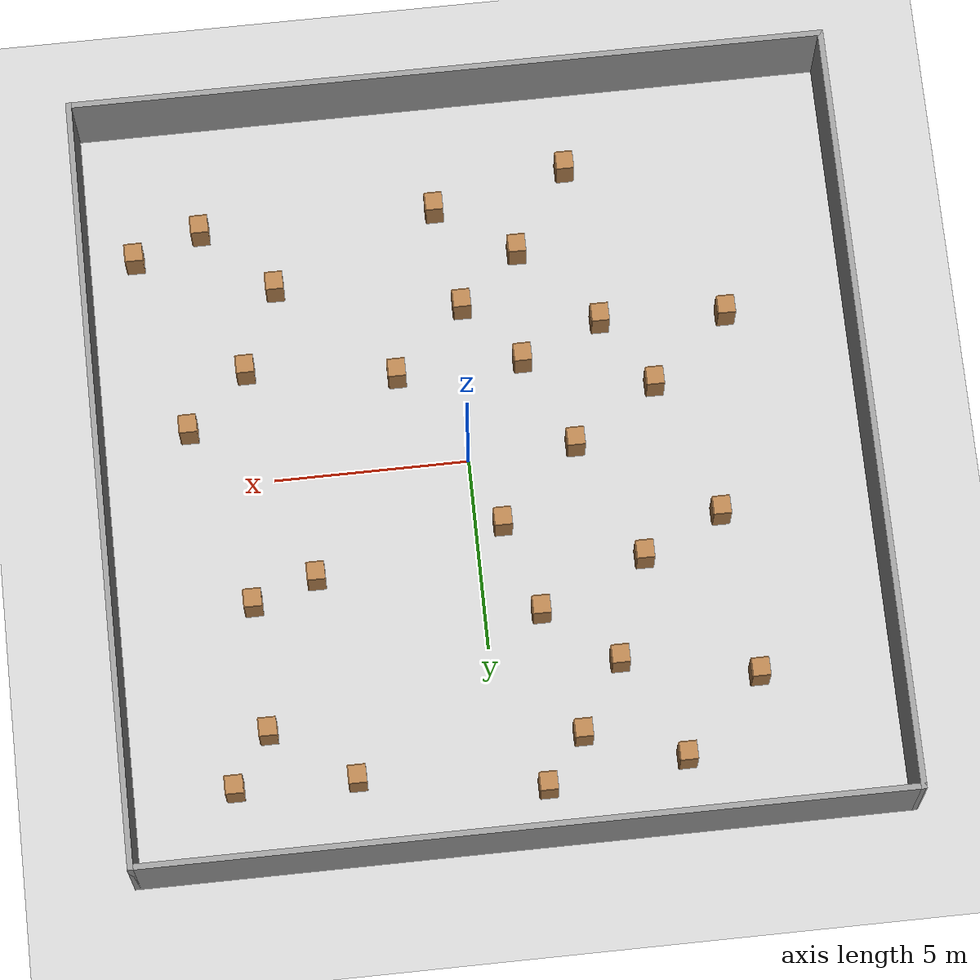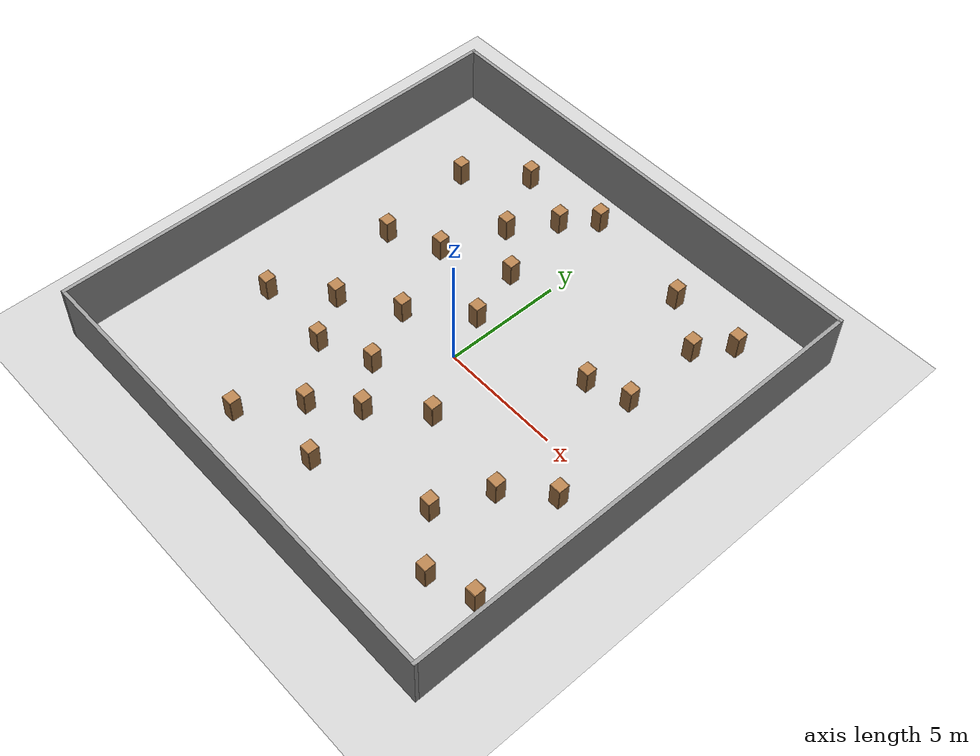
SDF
<sdf version="1.6">
 <world name="default">
  <light name="sun" type="directional">
   <pose>0 0 10 0 -0 0</pose>
   <diffuse>0.8 0.8 0.8 1</diffuse>
   <specular>0.2 0.2 0.2 1</specular>
   <attenuation>
    <range>1000</range>
    <constant>0.9</constant>
    <linear>0.01</linear>
    <quadratic>0.001</quadratic>
   </attenuation>
   <direction>-0.5 0.1 -0.9</direction>
  </light>
  <model name="ground_plane">
   <static>1</static>
   <link name="link">
    <collision name="collision">
     <geometry><plane><normal>0 0 1</normal><size>100 100</size></plane></geometry>
     <surface><friction><ode><mu>100</mu><mu2>50</mu2></ode></friction></surface>
    </collision>
    <visual name="visual">
     <cast_shadows>0</cast_shadows>
     <geometry><plane><normal>0 0 1</normal><size>100 100</size></plane></geometry>
     <material>
      <script><uri>file://media/materials/scripts/gazebo.material</uri><name>Gazebo/Grey</name></script>
     </material>
    </visual>
   </link>
  </model>
  <gravity>0 0 -9.8</gravity>
  <magnetic_field>6e-06 2.3e-05 -4.2e-05</magnetic_field>
  <atmosphere type="adiabatic"/>
  <physics name="default_physics" default="0" type="ode">
   <max_step_size>0.001</max_step_size>
   <real_time_factor>1</real_time_factor>
   <real_time_update_rate>1000</real_time_update_rate>
  </physics>
  <scene><ambient>0.4 0.4 0.4 1</ambient><background>0.7 0.7 0.7 1</background><shadows>1</shadows></scene>
  <audio><device>default</device></audio>
  <spherical_coordinates>
   <surface_model>EARTH_WGS84</surface_model>
   <latitude_deg>0</latitude_deg>
   <longitude_deg>0</longitude_deg>
   <elevation>0</elevation>
   <heading_deg>0</heading_deg>
  </spherical_coordinates>
  <model name="room">
   <pose>-0.435747 0.13788 0 0 -0 0</pose>
   <link name="Wall_0">
    <collision name="Wall_0_Collision">
     <geometry><box><size>19.75 0.15 2.5</size></box></geometry>
     <pose>0 0 1.25 0 -0 0</pose>
    </collision>
    <visual name="Wall_0_Visual">
     <pose>0 0 1.25 0 -0 0</pose>
     <geometry><box><size>19.75 0.15 2.5</size></box></geometry>
     <material>
      <script><uri>file://media/materials/scripts/gazebo.material</uri><name>Gazebo/Grey</name></script>
      <ambient>1 1 1 1</ambient>
     </material>
     <meta><layer>0</layer></meta>
    </visual>
    <pose>-0 -10.05 0 0 -0 3.14159</pose>
   </link>
   <link name="Wall_2">
    <collision name="Wall_2_Collision">
     <geometry><box><size>20.25 0.15 2.5</size></box></geometry>
     <pose>0 0 1.25 0 -0 0</pose>
    </collision>
    <visual name="Wall_2_Visual">
     <pose>0 0 1.25 0 -0 0</pose>
     <geometry><box><size>20.25 0.15 2.5</size></box></geometry>
     <material>
      <script><uri>file://media/materials/scripts/gazebo.material</uri><name>Gazebo/Grey</name></script>
      <ambient>1 1 1 1</ambient>
     </material>
     <meta><layer>0</layer></meta>
    </visual>
    <pose>-9.8 0 0 0 -0 1.5708</pose>
   </link>
   <link name="Wall_3">
    <collision name="Wall_3_Collision">
     <geometry><box><size>19.75 0.15 2.5</size></box></geometry>
     <pose>0 0 1.25 0 -0 0</pose>
    </collision>
    <visual name="Wall_3_Visual">
     <pose>0 0 1.25 0 -0 0</pose>
     <geometry><box><size>19.75 0.15 2.5</size></box></geometry>
     <material>
      <script><uri>file://media/materials/scripts/gazebo.material</uri><name>Gazebo/Grey</name></script>
      <ambient>1 1 1 1</ambient>
     </material>
     <meta><layer>0</layer></meta>
    </visual>
    <pose>-0 10.05 0 0 -0 0</pose>
   </link>
   <link name="Wall_4">
    <collision name="Wall_4_Collision">
     <geometry><box><size>20.25 0.15 2.5</size></box></geometry>
     <pose>0 0 1.25 0 -0 0</pose>
    </collision>
    <visual name="Wall_4_Visual">
     <pose>0 0 1.25 0 -0 0</pose>
     <geometry><box><size>20.25 0.15 2.5</size></box></geometry>
     <material>
      <script><uri>file://media/materials/scripts/gazebo.material</uri><name>Gazebo/Grey</name></script>
      <ambient>1 1 1 1</ambient>
     </material>
     <meta><layer>0</layer></meta>
    </visual>
    <pose>9.8 0 0 0 -0 -1.5708</pose>
   </link>
   <static>1</static>
  </model>
  <model name="cabinet">
   <static>1</static>
   <link name="cabinet_bottom_plate">
    <inertial>
     <pose>0 0 -1 0 -0 0</pose>
     <inertia><ixx>2.05</ixx><ixy>0</ixy><ixz>0</ixz><iyy>2.05</iyy><iyz>0</iyz><izz>2.05</izz></inertia>
     <mass>25</mass>
    </inertial>
    <collision name="cabinet_bottom_plate_geom">
     <pose>0 0 0.01 0 -0 0</pose>
     <geometry><box><size>0.45 0.45 0.02</size></box></geometry>
    </collision>
    <visual name="cabinet_bottom_plate_geom_visual">
     <pose>0 0 0.01 0 -0 0</pose>
     <geometry><box><size>0.45 0.45 0.02</size></box></geometry>
     <material>
      <script><uri>file://media/materials/scripts/gazebo.material</uri><name>Gazebo/Wood</name></script>
     </material>
    </visual>
    <collision name="cabinet_bottom_plate_geom_cabinet_back_plate">
     <pose>0.235 0 0.51 0 -0 0</pose>
     <geometry><box><size>0.02 0.45 1.02</size></box></geometry>
    </collision>
    <visual name="cabinet_bottom_plate_geom_cabinet_back_plate_visual">
     <pose>0.235 0 0.51 0 -0 0</pose>
     <geometry><box><size>0.02 0.45 1.02</size></box></geometry>
     <material>
      <script><uri>file://media/materials/scripts/gazebo.material</uri><name>Gazebo/Wood</name></script>
     </material>
    </visual>
    <collision name="cabinet_bottom_plate_geom_cabinet_left_plate">
     <pose>0 0.235 0.51 0 -0 0</pose>
     <geometry><box><size>0.45 0.02 1.02</size></box></geometry>
    </collision>
    <visual name="cabinet_bottom_plate_geom_cabinet_left_plate_visual">
     <pose>0 0.235 0.51 0 -0 0</pose>
     <geometry><box><size>0.45 0.02 1.02</size></box></geometry>
     <material>
      <script><uri>file://media/materials/scripts/gazebo.material</uri><name>Gazebo/Wood</name></script>
     </material>
    </visual>
    <collision name="cabinet_bottom_plate_geom_cabinet_middle_plate">
     <pose>0 0 0.51 0 -0 0</pose>
     <geometry><box><size>0.45 0.45 0.02</size></box></geometry>
    </collision>
    <visual name="cabinet_bottom_plate_geom_cabinet_middle_plate_visual">
     <pose>0 0 0.51 0 -0 0</pose>
     <geometry><box><size>0.45 0.45 0.02</size></box></geometry>
     <material>
      <script><uri>file://media/materials/scripts/gazebo.material</uri><name>Gazebo/Wood</name></script>
     </material>
    </visual>
    <collision name="cabinet_bottom_plate_geom_cabinet_right_plate">
     <pose>0 -0.235 0.51 0 -0 0</pose>
     <geometry><box><size>0.45 0.02 1.02</size></box></geometry>
    </collision>
    <visual name="cabinet_bottom_plate_geom_cabinet_right_plate_visual">
     <pose>0 -0.235 0.51 0 -0 0</pose>
     <geometry><box><size>0.45 0.02 1.02</size></box></geometry>
     <material>
      <script><uri>file://media/materials/scripts/gazebo.material</uri><name>Gazebo/Wood</name></script>
     </material>
    </visual>
    <collision name="cabinet_bottom_plate_geom_cabinet_top_plate">
     <pose>0 0 1.01 0 -0 0</pose>
     <geometry><box><size>0.45 0.45 0.02</size></box></geometry>
    </collision>
    <visual name="cabinet_bottom_plate_geom_cabinet_top_plate_visual">
     <pose>0 0 1.01 0 -0 0</pose>
     <geometry><box><size>0.45 0.45 0.02</size></box></geometry>
     <material>
      <script><uri>file://media/materials/scripts/gazebo.material</uri><name>Gazebo/Wood</name></script>
     </material>
    </visual>
   </link>
   <pose>6.71226 8.05087 0 0 -0 0</pose>
  </model>
  <model name="cabinet_0">
   <static>1</static>
   <link name="cabinet_bottom_plate">
    <inertial>
     <pose>0 0 -1 0 -0 0</pose>
     <inertia><ixx>2.05</ixx><ixy>0</ixy><ixz>0</ixz><iyy>2.05</iyy><iyz>0</iyz><izz>2.05</izz></inertia>
     <mass>25</mass>
    </inertial>
    <collision name="cabinet_bottom_plate_geom">
     <pose>0 0 0.01 0 -0 0</pose>
     <geometry><box><size>0.45 0.45 0.02</size></box></geometry>
    </collision>
    <visual name="cabinet_bottom_plate_geom_visual">
     <pose>0 0 0.01 0 -0 0</pose>
     <geometry><box><size>0.45 0.45 0.02</size></box></geometry>
     <material>
      <script><uri>file://media/materials/scripts/gazebo.material</uri><name>Gazebo/Wood</name></script>
     </material>
    </visual>
    <collision name="cabinet_bottom_plate_geom_cabinet_back_plate">
     <pose>0.235 0 0.51 0 -0 0</pose>
     <geometry><box><size>0.02 0.45 1.02</size></box></geometry>
    </collision>
    <visual name="cabinet_bottom_plate_geom_cabinet_back_plate_visual">
     <pose>0.235 0 0.51 0 -0 0</pose>
     <geometry><box><size>0.02 0.45 1.02</size></box></geometry>
     <material>
      <script><uri>file://media/materials/scripts/gazebo.material</uri><name>Gazebo/Wood</name></script>
     </material>
    </visual>
    <collision name="cabinet_bottom_plate_geom_cabinet_left_plate">
     <pose>0 0.235 0.51 0 -0 0</pose>
     <geometry><box><size>0.45 0.02 1.02</size></box></geometry>
    </collision>
    <visual name="cabinet_bottom_plate_geom_cabinet_left_plate_visual">
     <pose>0 0.235 0.51 0 -0 0</pose>
     <geometry><box><size>0.45 0.02 1.02</size></box></geometry>
     <material>
      <script><uri>file://media/materials/scripts/gazebo.material</uri><name>Gazebo/Wood</name></script>
     </material>
    </visual>
    <collision name="cabinet_bottom_plate_geom_cabinet_middle_plate">
     <pose>0 0 0.51 0 -0 0</pose>
     <geometry><box><size>0.45 0.45 0.02</size></box></geometry>
    </collision>
    <visual name="cabinet_bottom_plate_geom_cabinet_middle_plate_visual">
     <pose>0 0 0.51 0 -0 0</pose>
     <geometry><box><size>0.45 0.45 0.02</size></box></geometry>
     <material>
      <script><uri>file://media/materials/scripts/gazebo.material</uri><name>Gazebo/Wood</name></script>
     </material>
    </visual>
    <collision name="cabinet_bottom_plate_geom_cabinet_right_plate">
     <pose>0 -0.235 0.51 0 -0 0</pose>
     <geometry><box><size>0.45 0.02 1.02</size></box></geometry>
    </collision>
    <visual name="cabinet_bottom_plate_geom_cabinet_right_plate_visual">
     <pose>0 -0.235 0.51 0 -0 0</pose>
     <geometry><box><size>0.45 0.02 1.02</size></box></geometry>
     <material>
      <script><uri>file://media/materials/scripts/gazebo.material</uri><name>Gazebo/Wood</name></script>
     </material>
    </visual>
    <collision name="cabinet_bottom_plate_geom_cabinet_top_plate">
     <pose>0 0 1.01 0 -0 0</pose>
     <geometry><box><size>0.45 0.45 0.02</size></box></geometry>
    </collision>
    <visual name="cabinet_bottom_plate_geom_cabinet_top_plate_visual">
     <pose>0 0 1.01 0 -0 0</pose>
     <geometry><box><size>0.45 0.45 0.02</size></box></geometry>
     <material>
      <script><uri>file://media/materials/scripts/gazebo.material</uri><name>Gazebo/Wood</name></script>
     </material>
    </visual>
   </link>
   <pose>5.74581 6.66166 0 0 -0 0</pose>
  </model>
  <model name="cabinet_1">
   <static>1</static>
   <link name="cabinet_bottom_plate">
    <inertial>
     <pose>0 0 -1 0 -0 0</pose>
     <inertia><ixx>2.05</ixx><ixy>0</ixy><ixz>0</ixz><iyy>2.05</iyy><iyz>0</iyz><izz>2.05</izz></inertia>
     <mass>25</mass>
    </inertial>
    <collision name="cabinet_bottom_plate_geom">
     <pose>0 0 0.01 0 -0 0</pose>
     <geometry><box><size>0.45 0.45 0.02</size></box></geometry>
    </collision>
    <visual name="cabinet_bottom_plate_geom_visual">
     <pose>0 0 0.01 0 -0 0</pose>
     <geometry><box><size>0.45 0.45 0.02</size></box></geometry>
     <material>
      <script><uri>file://media/materials/scripts/gazebo.material</uri><name>Gazebo/Wood</name></script>
     </material>
    </visual>
    <collision name="cabinet_bottom_plate_geom_cabinet_back_plate">
     <pose>0.235 0 0.51 0 -0 0</pose>
     <geometry><box><size>0.02 0.45 1.02</size></box></geometry>
    </collision>
    <visual name="cabinet_bottom_plate_geom_cabinet_back_plate_visual">
     <pose>0.235 0 0.51 0 -0 0</pose>
     <geometry><box><size>0.02 0.45 1.02</size></box></geometry>
     <material>
      <script><uri>file://media/materials/scripts/gazebo.material</uri><name>Gazebo/Wood</name></script>
     </material>
    </visual>
    <collision name="cabinet_bottom_plate_geom_cabinet_left_plate">
     <pose>0 0.235 0.51 0 -0 0</pose>
     <geometry><box><size>0.45 0.02 1.02</size></box></geometry>
    </collision>
    <visual name="cabinet_bottom_plate_geom_cabinet_left_plate_visual">
     <pose>0 0.235 0.51 0 -0 0</pose>
     <geometry><box><size>0.45 0.02 1.02</size></box></geometry>
     <material>
      <script><uri>file://media/materials/scripts/gazebo.material</uri><name>Gazebo/Wood</name></script>
     </material>
    </visual>
    <collision name="cabinet_bottom_plate_geom_cabinet_middle_plate">
     <pose>0 0 0.51 0 -0 0</pose>
     <geometry><box><size>0.45 0.45 0.02</size></box></geometry>
    </collision>
    <visual name="cabinet_bottom_plate_geom_cabinet_middle_plate_visual">
     <pose>0 0 0.51 0 -0 0</pose>
     <geometry><box><size>0.45 0.45 0.02</size></box></geometry>
     <material>
      <script><uri>file://media/materials/scripts/gazebo.material</uri><name>Gazebo/Wood</name></script>
     </material>
    </visual>
    <collision name="cabinet_bottom_plate_geom_cabinet_right_plate">
     <pose>0 -0.235 0.51 0 -0 0</pose>
     <geometry><box><size>0.45 0.02 1.02</size></box></geometry>
    </collision>
    <visual name="cabinet_bottom_plate_geom_cabinet_right_plate_visual">
     <pose>0 -0.235 0.51 0 -0 0</pose>
     <geometry><box><size>0.45 0.02 1.02</size></box></geometry>
     <material>
      <script><uri>file://media/materials/scripts/gazebo.material</uri><name>Gazebo/Wood</name></script>
     </material>
    </visual>
    <collision name="cabinet_bottom_plate_geom_cabinet_top_plate">
     <pose>0 0 1.01 0 -0 0</pose>
     <geometry><box><size>0.45 0.45 0.02</size></box></geometry>
    </collision>
    <visual name="cabinet_bottom_plate_geom_cabinet_top_plate_visual">
     <pose>0 0 1.01 0 -0 0</pose>
     <geometry><box><size>0.45 0.45 0.02</size></box></geometry>
     <material>
      <script><uri>file://media/materials/scripts/gazebo.material</uri><name>Gazebo/Wood</name></script>
     </material>
    </visual>
   </link>
   <pose>3.61983 8.1036 0 0 -0 0</pose>
  </model>
  <model name="cabinet_2">
   <static>1</static>
   <link name="cabinet_bottom_plate">
    <inertial>
     <pose>0 0 -1 0 -0 0</pose>
     <inertia><ixx>2.05</ixx><ixy>0</ixy><ixz>0</ixz><iyy>2.05</iyy><iyz>0</iyz><izz>2.05</izz></inertia>
     <mass>25</mass>
    </inertial>
    <collision name="cabinet_bottom_plate_geom">
     <pose>0 0 0.01 0 -0 0</pose>
     <geometry><box><size>0.45 0.45 0.02</size></box></geometry>
    </collision>
    <visual name="cabinet_bottom_plate_geom_visual">
     <pose>0 0 0.01 0 -0 0</pose>
     <geometry><box><size>0.45 0.45 0.02</size></box></geometry>
     <material>
      <script><uri>file://media/materials/scripts/gazebo.material</uri><name>Gazebo/Wood</name></script>
     </material>
    </visual>
    <collision name="cabinet_bottom_plate_geom_cabinet_back_plate">
     <pose>0.235 0 0.51 0 -0 0</pose>
     <geometry><box><size>0.02 0.45 1.02</size></box></geometry>
    </collision>
    <visual name="cabinet_bottom_plate_geom_cabinet_back_plate_visual">
     <pose>0.235 0 0.51 0 -0 0</pose>
     <geometry><box><size>0.02 0.45 1.02</size></box></geometry>
     <material>
      <script><uri>file://media/materials/scripts/gazebo.material</uri><name>Gazebo/Wood</name></script>
     </material>
    </visual>
    <collision name="cabinet_bottom_plate_geom_cabinet_left_plate">
     <pose>0 0.235 0.51 0 -0 0</pose>
     <geometry><box><size>0.45 0.02 1.02</size></box></geometry>
    </collision>
    <visual name="cabinet_bottom_plate_geom_cabinet_left_plate_visual">
     <pose>0 0.235 0.51 0 -0 0</pose>
     <geometry><box><size>0.45 0.02 1.02</size></box></geometry>
     <material>
      <script><uri>file://media/materials/scripts/gazebo.material</uri><name>Gazebo/Wood</name></script>
     </material>
    </visual>
    <collision name="cabinet_bottom_plate_geom_cabinet_middle_plate">
     <pose>0 0 0.51 0 -0 0</pose>
     <geometry><box><size>0.45 0.45 0.02</size></box></geometry>
    </collision>
    <visual name="cabinet_bottom_plate_geom_cabinet_middle_plate_visual">
     <pose>0 0 0.51 0 -0 0</pose>
     <geometry><box><size>0.45 0.45 0.02</size></box></geometry>
     <material>
      <script><uri>file://media/materials/scripts/gazebo.material</uri><name>Gazebo/Wood</name></script>
     </material>
    </visual>
    <collision name="cabinet_bottom_plate_geom_cabinet_right_plate">
     <pose>0 -0.235 0.51 0 -0 0</pose>
     <geometry><box><size>0.45 0.02 1.02</size></box></geometry>
    </collision>
    <visual name="cabinet_bottom_plate_geom_cabinet_right_plate_visual">
     <pose>0 -0.235 0.51 0 -0 0</pose>
     <geometry><box><size>0.45 0.02 1.02</size></box></geometry>
     <material>
      <script><uri>file://media/materials/scripts/gazebo.material</uri><name>Gazebo/Wood</name></script>
     </material>
    </visual>
    <collision name="cabinet_bottom_plate_geom_cabinet_top_plate">
     <pose>0 0 1.01 0 -0 0</pose>
     <geometry><box><size>0.45 0.45 0.02</size></box></geometry>
    </collision>
    <visual name="cabinet_bottom_plate_geom_cabinet_top_plate_visual">
     <pose>0 0 1.01 0 -0 0</pose>
     <geometry><box><size>0.45 0.45 0.02</size></box></geometry>
     <material>
      <script><uri>file://media/materials/scripts/gazebo.material</uri><name>Gazebo/Wood</name></script>
     </material>
    </visual>
   </link>
   <pose>5.83049 3.29027 0 0 -0 0</pose>
  </model>
  <model name="cabinet_3">
   <static>1</static>
   <link name="cabinet_bottom_plate">
    <inertial>
     <pose>0 0 -1 0 -0 0</pose>
     <inertia><ixx>2.05</ixx><ixy>0</ixy><ixz>0</ixz><iyy>2.05</iyy><iyz>0</iyz><izz>2.05</izz></inertia>
     <mass>25</mass>
    </inertial>
    <collision name="cabinet_bottom_plate_geom">
     <pose>0 0 0.01 0 -0 0</pose>
     <geometry><box><size>0.45 0.45 0.02</size></box></geometry>
    </collision>
    <visual name="cabinet_bottom_plate_geom_visual">
     <pose>0 0 0.01 0 -0 0</pose>
     <geometry><box><size>0.45 0.45 0.02</size></box></geometry>
     <material>
      <script><uri>file://media/materials/scripts/gazebo.material</uri><name>Gazebo/Wood</name></script>
     </material>
    </visual>
    <collision name="cabinet_bottom_plate_geom_cabinet_back_plate">
     <pose>0.235 0 0.51 0 -0 0</pose>
     <geometry><box><size>0.02 0.45 1.02</size></box></geometry>
    </collision>
    <visual name="cabinet_bottom_plate_geom_cabinet_back_plate_visual">
     <pose>0.235 0 0.51 0 -0 0</pose>
     <geometry><box><size>0.02 0.45 1.02</size></box></geometry>
     <material>
      <script><uri>file://media/materials/scripts/gazebo.material</uri><name>Gazebo/Wood</name></script>
     </material>
    </visual>
    <collision name="cabinet_bottom_plate_geom_cabinet_left_plate">
     <pose>0 0.235 0.51 0 -0 0</pose>
     <geometry><box><size>0.45 0.02 1.02</size></box></geometry>
    </collision>
    <visual name="cabinet_bottom_plate_geom_cabinet_left_plate_visual">
     <pose>0 0.235 0.51 0 -0 0</pose>
     <geometry><box><size>0.45 0.02 1.02</size></box></geometry>
     <material>
      <script><uri>file://media/materials/scripts/gazebo.material</uri><name>Gazebo/Wood</name></script>
     </material>
    </visual>
    <collision name="cabinet_bottom_plate_geom_cabinet_middle_plate">
     <pose>0 0 0.51 0 -0 0</pose>
     <geometry><box><size>0.45 0.45 0.02</size></box></geometry>
    </collision>
    <visual name="cabinet_bottom_plate_geom_cabinet_middle_plate_visual">
     <pose>0 0 0.51 0 -0 0</pose>
     <geometry><box><size>0.45 0.45 0.02</size></box></geometry>
     <material>
      <script><uri>file://media/materials/scripts/gazebo.material</uri><name>Gazebo/Wood</name></script>
     </material>
    </visual>
    <collision name="cabinet_bottom_plate_geom_cabinet_right_plate">
     <pose>0 -0.235 0.51 0 -0 0</pose>
     <geometry><box><size>0.45 0.02 1.02</size></box></geometry>
    </collision>
    <visual name="cabinet_bottom_plate_geom_cabinet_right_plate_visual">
     <pose>0 -0.235 0.51 0 -0 0</pose>
     <geometry><box><size>0.45 0.02 1.02</size></box></geometry>
     <material>
      <script><uri>file://media/materials/scripts/gazebo.material</uri><name>Gazebo/Wood</name></script>
     </material>
    </visual>
    <collision name="cabinet_bottom_plate_geom_cabinet_top_plate">
     <pose>0 0 1.01 0 -0 0</pose>
     <geometry><box><size>0.45 0.45 0.02</size></box></geometry>
    </collision>
    <visual name="cabinet_bottom_plate_geom_cabinet_top_plate_visual">
     <pose>0 0 1.01 0 -0 0</pose>
     <geometry><box><size>0.45 0.45 0.02</size></box></geometry>
     <material>
      <script><uri>file://media/materials/scripts/gazebo.material</uri><name>Gazebo/Wood</name></script>
     </material>
    </visual>
   </link>
   <pose>7.07993 -1.47835 0 0 -0 0</pose>
  </model>
  <model name="cabinet_4">
   <static>1</static>
   <link name="cabinet_bottom_plate">
    <inertial>
     <pose>0 0 -1 0 -0 0</pose>
     <inertia><ixx>2.05</ixx><ixy>0</ixy><ixz>0</ixz><iyy>2.05</iyy><iyz>0</iyz><izz>2.05</izz></inertia>
     <mass>25</mass>
    </inertial>
    <collision name="cabinet_bottom_plate_geom">
     <pose>0 0 0.01 0 -0 0</pose>
     <geometry><box><size>0.45 0.45 0.02</size></box></geometry>
    </collision>
    <visual name="cabinet_bottom_plate_geom_visual">
     <pose>0 0 0.01 0 -0 0</pose>
     <geometry><box><size>0.45 0.45 0.02</size></box></geometry>
     <material>
      <script><uri>file://media/materials/scripts/gazebo.material</uri><name>Gazebo/Wood</name></script>
     </material>
    </visual>
    <collision name="cabinet_bottom_plate_geom_cabinet_back_plate">
     <pose>0.235 0 0.51 0 -0 0</pose>
     <geometry><box><size>0.02 0.45 1.02</size></box></geometry>
    </collision>
    <visual name="cabinet_bottom_plate_geom_cabinet_back_plate_visual">
     <pose>0.235 0 0.51 0 -0 0</pose>
     <geometry><box><size>0.02 0.45 1.02</size></box></geometry>
     <material>
      <script><uri>file://media/materials/scripts/gazebo.material</uri><name>Gazebo/Wood</name></script>
     </material>
    </visual>
    <collision name="cabinet_bottom_plate_geom_cabinet_left_plate">
     <pose>0 0.235 0.51 0 -0 0</pose>
     <geometry><box><size>0.45 0.02 1.02</size></box></geometry>
    </collision>
    <visual name="cabinet_bottom_plate_geom_cabinet_left_plate_visual">
     <pose>0 0.235 0.51 0 -0 0</pose>
     <geometry><box><size>0.45 0.02 1.02</size></box></geometry>
     <material>
      <script><uri>file://media/materials/scripts/gazebo.material</uri><name>Gazebo/Wood</name></script>
     </material>
    </visual>
    <collision name="cabinet_bottom_plate_geom_cabinet_middle_plate">
     <pose>0 0 0.51 0 -0 0</pose>
     <geometry><box><size>0.45 0.45 0.02</size></box></geometry>
    </collision>
    <visual name="cabinet_bottom_plate_geom_cabinet_middle_plate_visual">
     <pose>0 0 0.51 0 -0 0</pose>
     <geometry><box><size>0.45 0.45 0.02</size></box></geometry>
     <material>
      <script><uri>file://media/materials/scripts/gazebo.material</uri><name>Gazebo/Wood</name></script>
     </material>
    </visual>
    <collision name="cabinet_bottom_plate_geom_cabinet_right_plate">
     <pose>0 -0.235 0.51 0 -0 0</pose>
     <geometry><box><size>0.45 0.02 1.02</size></box></geometry>
    </collision>
    <visual name="cabinet_bottom_plate_geom_cabinet_right_plate_visual">
     <pose>0 -0.235 0.51 0 -0 0</pose>
     <geometry><box><size>0.45 0.02 1.02</size></box></geometry>
     <material>
      <script><uri>file://media/materials/scripts/gazebo.material</uri><name>Gazebo/Wood</name></script>
     </material>
    </visual>
    <collision name="cabinet_bottom_plate_geom_cabinet_top_plate">
     <pose>0 0 1.01 0 -0 0</pose>
     <geometry><box><size>0.45 0.45 0.02</size></box></geometry>
    </collision>
    <visual name="cabinet_bottom_plate_geom_cabinet_top_plate_visual">
     <pose>0 0 1.01 0 -0 0</pose>
     <geometry><box><size>0.45 0.45 0.02</size></box></geometry>
     <material>
      <script><uri>file://media/materials/scripts/gazebo.material</uri><name>Gazebo/Wood</name></script>
     </material>
    </visual>
   </link>
   <pose>8.0931 -6.2604 0 0 -0 0</pose>
  </model>
  <model name="cabinet_5">
   <static>1</static>
   <link name="cabinet_bottom_plate">
    <inertial>
     <pose>0 0 -1 0 -0 0</pose>
     <inertia><ixx>2.05</ixx><ixy>0</ixy><ixz>0</ixz><iyy>2.05</iyy><iyz>0</iyz><izz>2.05</izz></inertia>
     <mass>25</mass>
    </inertial>
    <collision name="cabinet_bottom_plate_geom">
     <pose>0 0 0.01 0 -0 0</pose>
     <geometry><box><size>0.45 0.45 0.02</size></box></geometry>
    </collision>
    <visual name="cabinet_bottom_plate_geom_visual">
     <pose>0 0 0.01 0 -0 0</pose>
     <geometry><box><size>0.45 0.45 0.02</size></box></geometry>
     <material>
      <script><uri>file://media/materials/scripts/gazebo.material</uri><name>Gazebo/Wood</name></script>
     </material>
    </visual>
    <collision name="cabinet_bottom_plate_geom_cabinet_back_plate">
     <pose>0.235 0 0.51 0 -0 0</pose>
     <geometry><box><size>0.02 0.45 1.02</size></box></geometry>
    </collision>
    <visual name="cabinet_bottom_plate_geom_cabinet_back_plate_visual">
     <pose>0.235 0 0.51 0 -0 0</pose>
     <geometry><box><size>0.02 0.45 1.02</size></box></geometry>
     <material>
      <script><uri>file://media/materials/scripts/gazebo.material</uri><name>Gazebo/Wood</name></script>
     </material>
    </visual>
    <collision name="cabinet_bottom_plate_geom_cabinet_left_plate">
     <pose>0 0.235 0.51 0 -0 0</pose>
     <geometry><box><size>0.45 0.02 1.02</size></box></geometry>
    </collision>
    <visual name="cabinet_bottom_plate_geom_cabinet_left_plate_visual">
     <pose>0 0.235 0.51 0 -0 0</pose>
     <geometry><box><size>0.45 0.02 1.02</size></box></geometry>
     <material>
      <script><uri>file://media/materials/scripts/gazebo.material</uri><name>Gazebo/Wood</name></script>
     </material>
    </visual>
    <collision name="cabinet_bottom_plate_geom_cabinet_middle_plate">
     <pose>0 0 0.51 0 -0 0</pose>
     <geometry><box><size>0.45 0.45 0.02</size></box></geometry>
    </collision>
    <visual name="cabinet_bottom_plate_geom_cabinet_middle_plate_visual">
     <pose>0 0 0.51 0 -0 0</pose>
     <geometry><box><size>0.45 0.45 0.02</size></box></geometry>
     <material>
      <script><uri>file://media/materials/scripts/gazebo.material</uri><name>Gazebo/Wood</name></script>
     </material>
    </visual>
    <collision name="cabinet_bottom_plate_geom_cabinet_right_plate">
     <pose>0 -0.235 0.51 0 -0 0</pose>
     <geometry><box><size>0.45 0.02 1.02</size></box></geometry>
    </collision>
    <visual name="cabinet_bottom_plate_geom_cabinet_right_plate_visual">
     <pose>0 -0.235 0.51 0 -0 0</pose>
     <geometry><box><size>0.45 0.02 1.02</size></box></geometry>
     <material>
      <script><uri>file://media/materials/scripts/gazebo.material</uri><name>Gazebo/Wood</name></script>
     </material>
    </visual>
    <collision name="cabinet_bottom_plate_geom_cabinet_top_plate">
     <pose>0 0 1.01 0 -0 0</pose>
     <geometry><box><size>0.45 0.45 0.02</size></box></geometry>
    </collision>
    <visual name="cabinet_bottom_plate_geom_cabinet_top_plate_visual">
     <pose>0 0 1.01 0 -0 0</pose>
     <geometry><box><size>0.45 0.45 0.02</size></box></geometry>
     <material>
      <script><uri>file://media/materials/scripts/gazebo.material</uri><name>Gazebo/Wood</name></script>
     </material>
    </visual>
   </link>
   <pose>5.48638 -2.93492 0 0 -0 0</pose>
  </model>
  <model name="cabinet_6">
   <static>1</static>
   <link name="cabinet_bottom_plate">
    <inertial>
     <pose>0 0 -1 0 -0 0</pose>
     <inertia><ixx>2.05</ixx><ixy>0</ixy><ixz>0</ixz><iyy>2.05</iyy><iyz>0</iyz><izz>2.05</izz></inertia>
     <mass>25</mass>
    </inertial>
    <collision name="cabinet_bottom_plate_geom">
     <pose>0 0 0.01 0 -0 0</pose>
     <geometry><box><size>0.45 0.45 0.02</size></box></geometry>
    </collision>
    <visual name="cabinet_bottom_plate_geom_visual">
     <pose>0 0 0.01 0 -0 0</pose>
     <geometry><box><size>0.45 0.45 0.02</size></box></geometry>
     <material>
      <script><uri>file://media/materials/scripts/gazebo.material</uri><name>Gazebo/Wood</name></script>
     </material>
    </visual>
    <collision name="cabinet_bottom_plate_geom_cabinet_back_plate">
     <pose>0.235 0 0.51 0 -0 0</pose>
     <geometry><box><size>0.02 0.45 1.02</size></box></geometry>
    </collision>
    <visual name="cabinet_bottom_plate_geom_cabinet_back_plate_visual">
     <pose>0.235 0 0.51 0 -0 0</pose>
     <geometry><box><size>0.02 0.45 1.02</size></box></geometry>
     <material>
      <script><uri>file://media/materials/scripts/gazebo.material</uri><name>Gazebo/Wood</name></script>
     </material>
    </visual>
    <collision name="cabinet_bottom_plate_geom_cabinet_left_plate">
     <pose>0 0.235 0.51 0 -0 0</pose>
     <geometry><box><size>0.45 0.02 1.02</size></box></geometry>
    </collision>
    <visual name="cabinet_bottom_plate_geom_cabinet_left_plate_visual">
     <pose>0 0.235 0.51 0 -0 0</pose>
     <geometry><box><size>0.45 0.02 1.02</size></box></geometry>
     <material>
      <script><uri>file://media/materials/scripts/gazebo.material</uri><name>Gazebo/Wood</name></script>
     </material>
    </visual>
    <collision name="cabinet_bottom_plate_geom_cabinet_middle_plate">
     <pose>0 0 0.51 0 -0 0</pose>
     <geometry><box><size>0.45 0.45 0.02</size></box></geometry>
    </collision>
    <visual name="cabinet_bottom_plate_geom_cabinet_middle_plate_visual">
     <pose>0 0 0.51 0 -0 0</pose>
     <geometry><box><size>0.45 0.45 0.02</size></box></geometry>
     <material>
      <script><uri>file://media/materials/scripts/gazebo.material</uri><name>Gazebo/Wood</name></script>
     </material>
    </visual>
    <collision name="cabinet_bottom_plate_geom_cabinet_right_plate">
     <pose>0 -0.235 0.51 0 -0 0</pose>
     <geometry><box><size>0.45 0.02 1.02</size></box></geometry>
    </collision>
    <visual name="cabinet_bottom_plate_geom_cabinet_right_plate_visual">
     <pose>0 -0.235 0.51 0 -0 0</pose>
     <geometry><box><size>0.45 0.02 1.02</size></box></geometry>
     <material>
      <script><uri>file://media/materials/scripts/gazebo.material</uri><name>Gazebo/Wood</name></script>
     </material>
    </visual>
    <collision name="cabinet_bottom_plate_geom_cabinet_top_plate">
     <pose>0 0 1.01 0 -0 0</pose>
     <geometry><box><size>0.45 0.45 0.02</size></box></geometry>
    </collision>
    <visual name="cabinet_bottom_plate_geom_cabinet_top_plate_visual">
     <pose>0 0 1.01 0 -0 0</pose>
     <geometry><box><size>0.45 0.45 0.02</size></box></geometry>
     <material>
      <script><uri>file://media/materials/scripts/gazebo.material</uri><name>Gazebo/Wood</name></script>
     </material>
    </visual>
   </link>
   <pose>4.53058 -5.11799 0 0 -0 0</pose>
  </model>
  <model name="cabinet_7">
   <static>1</static>
   <link name="cabinet_bottom_plate">
    <inertial>
     <pose>0 0 -1 0 -0 0</pose>
     <inertia><ixx>2.05</ixx><ixy>0</ixy><ixz>0</ixz><iyy>2.05</iyy><iyz>0</iyz><izz>2.05</izz></inertia>
     <mass>25</mass>
    </inertial>
    <collision name="cabinet_bottom_plate_geom">
     <pose>0 0 0.01 0 -0 0</pose>
     <geometry><box><size>0.45 0.45 0.02</size></box></geometry>
    </collision>
    <visual name="cabinet_bottom_plate_geom_visual">
     <pose>0 0 0.01 0 -0 0</pose>
     <geometry><box><size>0.45 0.45 0.02</size></box></geometry>
     <material>
      <script><uri>file://media/materials/scripts/gazebo.material</uri><name>Gazebo/Wood</name></script>
     </material>
    </visual>
    <collision name="cabinet_bottom_plate_geom_cabinet_back_plate">
     <pose>0.235 0 0.51 0 -0 0</pose>
     <geometry><box><size>0.02 0.45 1.02</size></box></geometry>
    </collision>
    <visual name="cabinet_bottom_plate_geom_cabinet_back_plate_visual">
     <pose>0.235 0 0.51 0 -0 0</pose>
     <geometry><box><size>0.02 0.45 1.02</size></box></geometry>
     <material>
      <script><uri>file://media/materials/scripts/gazebo.material</uri><name>Gazebo/Wood</name></script>
     </material>
    </visual>
    <collision name="cabinet_bottom_plate_geom_cabinet_left_plate">
     <pose>0 0.235 0.51 0 -0 0</pose>
     <geometry><box><size>0.45 0.02 1.02</size></box></geometry>
    </collision>
    <visual name="cabinet_bottom_plate_geom_cabinet_left_plate_visual">
     <pose>0 0.235 0.51 0 -0 0</pose>
     <geometry><box><size>0.45 0.02 1.02</size></box></geometry>
     <material>
      <script><uri>file://media/materials/scripts/gazebo.material</uri><name>Gazebo/Wood</name></script>
     </material>
    </visual>
    <collision name="cabinet_bottom_plate_geom_cabinet_middle_plate">
     <pose>0 0 0.51 0 -0 0</pose>
     <geometry><box><size>0.45 0.45 0.02</size></box></geometry>
    </collision>
    <visual name="cabinet_bottom_plate_geom_cabinet_middle_plate_visual">
     <pose>0 0 0.51 0 -0 0</pose>
     <geometry><box><size>0.45 0.45 0.02</size></box></geometry>
     <material>
      <script><uri>file://media/materials/scripts/gazebo.material</uri><name>Gazebo/Wood</name></script>
     </material>
    </visual>
    <collision name="cabinet_bottom_plate_geom_cabinet_right_plate">
     <pose>0 -0.235 0.51 0 -0 0</pose>
     <geometry><box><size>0.45 0.02 1.02</size></box></geometry>
    </collision>
    <visual name="cabinet_bottom_plate_geom_cabinet_right_plate_visual">
     <pose>0 -0.235 0.51 0 -0 0</pose>
     <geometry><box><size>0.45 0.02 1.02</size></box></geometry>
     <material>
      <script><uri>file://media/materials/scripts/gazebo.material</uri><name>Gazebo/Wood</name></script>
     </material>
    </visual>
    <collision name="cabinet_bottom_plate_geom_cabinet_top_plate">
     <pose>0 0 1.01 0 -0 0</pose>
     <geometry><box><size>0.45 0.45 0.02</size></box></geometry>
    </collision>
    <visual name="cabinet_bottom_plate_geom_cabinet_top_plate_visual">
     <pose>0 0 1.01 0 -0 0</pose>
     <geometry><box><size>0.45 0.45 0.02</size></box></geometry>
     <material>
      <script><uri>file://media/materials/scripts/gazebo.material</uri><name>Gazebo/Wood</name></script>
     </material>
    </visual>
   </link>
   <pose>4.17053 2.75304 0 0 -0 0</pose>
  </model>
  <model name="cabinet_8">
   <static>1</static>
   <link name="cabinet_bottom_plate">
    <inertial>
     <pose>0 0 -1 0 -0 0</pose>
     <inertia><ixx>2.05</ixx><ixy>0</ixy><ixz>0</ixz><iyy>2.05</iyy><iyz>0</iyz><izz>2.05</izz></inertia>
     <mass>25</mass>
    </inertial>
    <collision name="cabinet_bottom_plate_geom">
     <pose>0 0 0.01 0 -0 0</pose>
     <geometry><box><size>0.45 0.45 0.02</size></box></geometry>
    </collision>
    <visual name="cabinet_bottom_plate_geom_visual">
     <pose>0 0 0.01 0 -0 0</pose>
     <geometry><box><size>0.45 0.45 0.02</size></box></geometry>
     <material>
      <script><uri>file://media/materials/scripts/gazebo.material</uri><name>Gazebo/Wood</name></script>
     </material>
    </visual>
    <collision name="cabinet_bottom_plate_geom_cabinet_back_plate">
     <pose>0.235 0 0.51 0 -0 0</pose>
     <geometry><box><size>0.02 0.45 1.02</size></box></geometry>
    </collision>
    <visual name="cabinet_bottom_plate_geom_cabinet_back_plate_visual">
     <pose>0.235 0 0.51 0 -0 0</pose>
     <geometry><box><size>0.02 0.45 1.02</size></box></geometry>
     <material>
      <script><uri>file://media/materials/scripts/gazebo.material</uri><name>Gazebo/Wood</name></script>
     </material>
    </visual>
    <collision name="cabinet_bottom_plate_geom_cabinet_left_plate">
     <pose>0 0.235 0.51 0 -0 0</pose>
     <geometry><box><size>0.45 0.02 1.02</size></box></geometry>
    </collision>
    <visual name="cabinet_bottom_plate_geom_cabinet_left_plate_visual">
     <pose>0 0.235 0.51 0 -0 0</pose>
     <geometry><box><size>0.45 0.02 1.02</size></box></geometry>
     <material>
      <script><uri>file://media/materials/scripts/gazebo.material</uri><name>Gazebo/Wood</name></script>
     </material>
    </visual>
    <collision name="cabinet_bottom_plate_geom_cabinet_middle_plate">
     <pose>0 0 0.51 0 -0 0</pose>
     <geometry><box><size>0.45 0.45 0.02</size></box></geometry>
    </collision>
    <visual name="cabinet_bottom_plate_geom_cabinet_middle_plate_visual">
     <pose>0 0 0.51 0 -0 0</pose>
     <geometry><box><size>0.45 0.45 0.02</size></box></geometry>
     <material>
      <script><uri>file://media/materials/scripts/gazebo.material</uri><name>Gazebo/Wood</name></script>
     </material>
    </visual>
    <collision name="cabinet_bottom_plate_geom_cabinet_right_plate">
     <pose>0 -0.235 0.51 0 -0 0</pose>
     <geometry><box><size>0.45 0.02 1.02</size></box></geometry>
    </collision>
    <visual name="cabinet_bottom_plate_geom_cabinet_right_plate_visual">
     <pose>0 -0.235 0.51 0 -0 0</pose>
     <geometry><box><size>0.45 0.02 1.02</size></box></geometry>
     <material>
      <script><uri>file://media/materials/scripts/gazebo.material</uri><name>Gazebo/Wood</name></script>
     </material>
    </visual>
    <collision name="cabinet_bottom_plate_geom_cabinet_top_plate">
     <pose>0 0 1.01 0 -0 0</pose>
     <geometry><box><size>0.45 0.45 0.02</size></box></geometry>
    </collision>
    <visual name="cabinet_bottom_plate_geom_cabinet_top_plate_visual">
     <pose>0 0 1.01 0 -0 0</pose>
     <geometry><box><size>0.45 0.45 0.02</size></box></geometry>
     <material>
      <script><uri>file://media/materials/scripts/gazebo.material</uri><name>Gazebo/Wood</name></script>
     </material>
    </visual>
   </link>
   <pose>6.33507 -6.86628 0 0 -0 0</pose>
  </model>
  <model name="cabinet_9">
   <static>1</static>
   <link name="cabinet_bottom_plate">
    <inertial>
     <pose>0 0 -1 0 -0 0</pose>
     <inertia><ixx>2.05</ixx><ixy>0</ixy><ixz>0</ixz><iyy>2.05</iyy><iyz>0</iyz><izz>2.05</izz></inertia>
     <mass>25</mass>
    </inertial>
    <collision name="cabinet_bottom_plate_geom">
     <pose>0 0 0.01 0 -0 0</pose>
     <geometry><box><size>0.45 0.45 0.02</size></box></geometry>
    </collision>
    <visual name="cabinet_bottom_plate_geom_visual">
     <pose>0 0 0.01 0 -0 0</pose>
     <geometry><box><size>0.45 0.45 0.02</size></box></geometry>
     <material>
      <script><uri>file://media/materials/scripts/gazebo.material</uri><name>Gazebo/Wood</name></script>
     </material>
    </visual>
    <collision name="cabinet_bottom_plate_geom_cabinet_back_plate">
     <pose>0.235 0 0.51 0 -0 0</pose>
     <geometry><box><size>0.02 0.45 1.02</size></box></geometry>
    </collision>
    <visual name="cabinet_bottom_plate_geom_cabinet_back_plate_visual">
     <pose>0.235 0 0.51 0 -0 0</pose>
     <geometry><box><size>0.02 0.45 1.02</size></box></geometry>
     <material>
      <script><uri>file://media/materials/scripts/gazebo.material</uri><name>Gazebo/Wood</name></script>
     </material>
    </visual>
    <collision name="cabinet_bottom_plate_geom_cabinet_left_plate">
     <pose>0 0.235 0.51 0 -0 0</pose>
     <geometry><box><size>0.45 0.02 1.02</size></box></geometry>
    </collision>
    <visual name="cabinet_bottom_plate_geom_cabinet_left_plate_visual">
     <pose>0 0.235 0.51 0 -0 0</pose>
     <geometry><box><size>0.45 0.02 1.02</size></box></geometry>
     <material>
      <script><uri>file://media/materials/scripts/gazebo.material</uri><name>Gazebo/Wood</name></script>
     </material>
    </visual>
    <collision name="cabinet_bottom_plate_geom_cabinet_middle_plate">
     <pose>0 0 0.51 0 -0 0</pose>
     <geometry><box><size>0.45 0.45 0.02</size></box></geometry>
    </collision>
    <visual name="cabinet_bottom_plate_geom_cabinet_middle_plate_visual">
     <pose>0 0 0.51 0 -0 0</pose>
     <geometry><box><size>0.45 0.45 0.02</size></box></geometry>
     <material>
      <script><uri>file://media/materials/scripts/gazebo.material</uri><name>Gazebo/Wood</name></script>
     </material>
    </visual>
    <collision name="cabinet_bottom_plate_geom_cabinet_right_plate">
     <pose>0 -0.235 0.51 0 -0 0</pose>
     <geometry><box><size>0.45 0.02 1.02</size></box></geometry>
    </collision>
    <visual name="cabinet_bottom_plate_geom_cabinet_right_plate_visual">
     <pose>0 -0.235 0.51 0 -0 0</pose>
     <geometry><box><size>0.45 0.02 1.02</size></box></geometry>
     <material>
      <script><uri>file://media/materials/scripts/gazebo.material</uri><name>Gazebo/Wood</name></script>
     </material>
    </visual>
    <collision name="cabinet_bottom_plate_geom_cabinet_top_plate">
     <pose>0 0 1.01 0 -0 0</pose>
     <geometry><box><size>0.45 0.45 0.02</size></box></geometry>
    </collision>
    <visual name="cabinet_bottom_plate_geom_cabinet_top_plate_visual">
     <pose>0 0 1.01 0 -0 0</pose>
     <geometry><box><size>0.45 0.45 0.02</size></box></geometry>
     <material>
      <script><uri>file://media/materials/scripts/gazebo.material</uri><name>Gazebo/Wood</name></script>
     </material>
    </visual>
   </link>
   <pose>-1.12707 8.77513 0 0 -0 0</pose>
  </model>
  <model name="cabinet_10">
   <static>1</static>
   <link name="cabinet_bottom_plate">
    <inertial>
     <pose>0 0 -1 0 -0 0</pose>
     <inertia><ixx>2.05</ixx><ixy>0</ixy><ixz>0</ixz><iyy>2.05</iyy><iyz>0</iyz><izz>2.05</izz></inertia>
     <mass>25</mass>
    </inertial>
    <collision name="cabinet_bottom_plate_geom">
     <pose>0 0 0.01 0 -0 0</pose>
     <geometry><box><size>0.45 0.45 0.02</size></box></geometry>
    </collision>
    <visual name="cabinet_bottom_plate_geom_visual">
     <pose>0 0 0.01 0 -0 0</pose>
     <geometry><box><size>0.45 0.45 0.02</size></box></geometry>
     <material>
      <script><uri>file://media/materials/scripts/gazebo.material</uri><name>Gazebo/Wood</name></script>
     </material>
    </visual>
    <collision name="cabinet_bottom_plate_geom_cabinet_back_plate">
     <pose>0.235 0 0.51 0 -0 0</pose>
     <geometry><box><size>0.02 0.45 1.02</size></box></geometry>
    </collision>
    <visual name="cabinet_bottom_plate_geom_cabinet_back_plate_visual">
     <pose>0.235 0 0.51 0 -0 0</pose>
     <geometry><box><size>0.02 0.45 1.02</size></box></geometry>
     <material>
      <script><uri>file://media/materials/scripts/gazebo.material</uri><name>Gazebo/Wood</name></script>
     </material>
    </visual>
    <collision name="cabinet_bottom_plate_geom_cabinet_left_plate">
     <pose>0 0.235 0.51 0 -0 0</pose>
     <geometry><box><size>0.45 0.02 1.02</size></box></geometry>
    </collision>
    <visual name="cabinet_bottom_plate_geom_cabinet_left_plate_visual">
     <pose>0 0.235 0.51 0 -0 0</pose>
     <geometry><box><size>0.45 0.02 1.02</size></box></geometry>
     <material>
      <script><uri>file://media/materials/scripts/gazebo.material</uri><name>Gazebo/Wood</name></script>
     </material>
    </visual>
    <collision name="cabinet_bottom_plate_geom_cabinet_middle_plate">
     <pose>0 0 0.51 0 -0 0</pose>
     <geometry><box><size>0.45 0.45 0.02</size></box></geometry>
    </collision>
    <visual name="cabinet_bottom_plate_geom_cabinet_middle_plate_visual">
     <pose>0 0 0.51 0 -0 0</pose>
     <geometry><box><size>0.45 0.45 0.02</size></box></geometry>
     <material>
      <script><uri>file://media/materials/scripts/gazebo.material</uri><name>Gazebo/Wood</name></script>
     </material>
    </visual>
    <collision name="cabinet_bottom_plate_geom_cabinet_right_plate">
     <pose>0 -0.235 0.51 0 -0 0</pose>
     <geometry><box><size>0.45 0.02 1.02</size></box></geometry>
    </collision>
    <visual name="cabinet_bottom_plate_geom_cabinet_right_plate_visual">
     <pose>0 -0.235 0.51 0 -0 0</pose>
     <geometry><box><size>0.45 0.02 1.02</size></box></geometry>
     <material>
      <script><uri>file://media/materials/scripts/gazebo.material</uri><name>Gazebo/Wood</name></script>
     </material>
    </visual>
    <collision name="cabinet_bottom_plate_geom_cabinet_top_plate">
     <pose>0 0 1.01 0 -0 0</pose>
     <geometry><box><size>0.45 0.45 0.02</size></box></geometry>
    </collision>
    <visual name="cabinet_bottom_plate_geom_cabinet_top_plate_visual">
     <pose>0 0 1.01 0 -0 0</pose>
     <geometry><box><size>0.45 0.45 0.02</size></box></geometry>
     <material>
      <script><uri>file://media/materials/scripts/gazebo.material</uri><name>Gazebo/Wood</name></script>
     </material>
    </visual>
   </link>
   <pose>-2.14834 7.51107 0 0 -0 0</pose>
  </model>
  <model name="cabinet_11">
   <static>1</static>
   <link name="cabinet_bottom_plate">
    <inertial>
     <pose>0 0 -1 0 -0 0</pose>
     <inertia><ixx>2.05</ixx><ixy>0</ixy><ixz>0</ixz><iyy>2.05</iyy><iyz>0</iyz><izz>2.05</izz></inertia>
     <mass>25</mass>
    </inertial>
    <collision name="cabinet_bottom_plate_geom">
     <pose>0 0 0.01 0 -0 0</pose>
     <geometry><box><size>0.45 0.45 0.02</size></box></geometry>
    </collision>
    <visual name="cabinet_bottom_plate_geom_visual">
     <pose>0 0 0.01 0 -0 0</pose>
     <geometry><box><size>0.45 0.45 0.02</size></box></geometry>
     <material>
      <script><uri>file://media/materials/scripts/gazebo.material</uri><name>Gazebo/Wood</name></script>
     </material>
    </visual>
    <collision name="cabinet_bottom_plate_geom_cabinet_back_plate">
     <pose>0.235 0 0.51 0 -0 0</pose>
     <geometry><box><size>0.02 0.45 1.02</size></box></geometry>
    </collision>
    <visual name="cabinet_bottom_plate_geom_cabinet_back_plate_visual">
     <pose>0.235 0 0.51 0 -0 0</pose>
     <geometry><box><size>0.02 0.45 1.02</size></box></geometry>
     <material>
      <script><uri>file://media/materials/scripts/gazebo.material</uri><name>Gazebo/Wood</name></script>
     </material>
    </visual>
    <collision name="cabinet_bottom_plate_geom_cabinet_left_plate">
     <pose>0 0.235 0.51 0 -0 0</pose>
     <geometry><box><size>0.45 0.02 1.02</size></box></geometry>
    </collision>
    <visual name="cabinet_bottom_plate_geom_cabinet_left_plate_visual">
     <pose>0 0.235 0.51 0 -0 0</pose>
     <geometry><box><size>0.45 0.02 1.02</size></box></geometry>
     <material>
      <script><uri>file://media/materials/scripts/gazebo.material</uri><name>Gazebo/Wood</name></script>
     </material>
    </visual>
    <collision name="cabinet_bottom_plate_geom_cabinet_middle_plate">
     <pose>0 0 0.51 0 -0 0</pose>
     <geometry><box><size>0.45 0.45 0.02</size></box></geometry>
    </collision>
    <visual name="cabinet_bottom_plate_geom_cabinet_middle_plate_visual">
     <pose>0 0 0.51 0 -0 0</pose>
     <geometry><box><size>0.45 0.45 0.02</size></box></geometry>
     <material>
      <script><uri>file://media/materials/scripts/gazebo.material</uri><name>Gazebo/Wood</name></script>
     </material>
    </visual>
    <collision name="cabinet_bottom_plate_geom_cabinet_right_plate">
     <pose>0 -0.235 0.51 0 -0 0</pose>
     <geometry><box><size>0.45 0.02 1.02</size></box></geometry>
    </collision>
    <visual name="cabinet_bottom_plate_geom_cabinet_right_plate_visual">
     <pose>0 -0.235 0.51 0 -0 0</pose>
     <geometry><box><size>0.45 0.02 1.02</size></box></geometry>
     <material>
      <script><uri>file://media/materials/scripts/gazebo.material</uri><name>Gazebo/Wood</name></script>
     </material>
    </visual>
    <collision name="cabinet_bottom_plate_geom_cabinet_top_plate">
     <pose>0 0 1.01 0 -0 0</pose>
     <geometry><box><size>0.45 0.45 0.02</size></box></geometry>
    </collision>
    <visual name="cabinet_bottom_plate_geom_cabinet_top_plate_visual">
     <pose>0 0 1.01 0 -0 0</pose>
     <geometry><box><size>0.45 0.45 0.02</size></box></geometry>
     <material>
      <script><uri>file://media/materials/scripts/gazebo.material</uri><name>Gazebo/Wood</name></script>
     </material>
    </visual>
   </link>
   <pose>-3.28339 5.70512 0 0 -0 0</pose>
  </model>
  <model name="cabinet_12">
   <static>1</static>
   <link name="cabinet_bottom_plate">
    <inertial>
     <pose>0 0 -1 0 -0 0</pose>
     <inertia><ixx>2.05</ixx><ixy>0</ixy><ixz>0</ixz><iyy>2.05</iyy><iyz>0</iyz><izz>2.05</izz></inertia>
     <mass>25</mass>
    </inertial>
    <collision name="cabinet_bottom_plate_geom">
     <pose>0 0 0.01 0 -0 0</pose>
     <geometry><box><size>0.45 0.45 0.02</size></box></geometry>
    </collision>
    <visual name="cabinet_bottom_plate_geom_visual">
     <pose>0 0 0.01 0 -0 0</pose>
     <geometry><box><size>0.45 0.45 0.02</size></box></geometry>
     <material>
      <script><uri>file://media/materials/scripts/gazebo.material</uri><name>Gazebo/Wood</name></script>
     </material>
    </visual>
    <collision name="cabinet_bottom_plate_geom_cabinet_back_plate">
     <pose>0.235 0 0.51 0 -0 0</pose>
     <geometry><box><size>0.02 0.45 1.02</size></box></geometry>
    </collision>
    <visual name="cabinet_bottom_plate_geom_cabinet_back_plate_visual">
     <pose>0.235 0 0.51 0 -0 0</pose>
     <geometry><box><size>0.02 0.45 1.02</size></box></geometry>
     <material>
      <script><uri>file://media/materials/scripts/gazebo.material</uri><name>Gazebo/Wood</name></script>
     </material>
    </visual>
    <collision name="cabinet_bottom_plate_geom_cabinet_left_plate">
     <pose>0 0.235 0.51 0 -0 0</pose>
     <geometry><box><size>0.45 0.02 1.02</size></box></geometry>
    </collision>
    <visual name="cabinet_bottom_plate_geom_cabinet_left_plate_visual">
     <pose>0 0.235 0.51 0 -0 0</pose>
     <geometry><box><size>0.45 0.02 1.02</size></box></geometry>
     <material>
      <script><uri>file://media/materials/scripts/gazebo.material</uri><name>Gazebo/Wood</name></script>
     </material>
    </visual>
    <collision name="cabinet_bottom_plate_geom_cabinet_middle_plate">
     <pose>0 0 0.51 0 -0 0</pose>
     <geometry><box><size>0.45 0.45 0.02</size></box></geometry>
    </collision>
    <visual name="cabinet_bottom_plate_geom_cabinet_middle_plate_visual">
     <pose>0 0 0.51 0 -0 0</pose>
     <geometry><box><size>0.45 0.45 0.02</size></box></geometry>
     <material>
      <script><uri>file://media/materials/scripts/gazebo.material</uri><name>Gazebo/Wood</name></script>
     </material>
    </visual>
    <collision name="cabinet_bottom_plate_geom_cabinet_right_plate">
     <pose>0 -0.235 0.51 0 -0 0</pose>
     <geometry><box><size>0.45 0.02 1.02</size></box></geometry>
    </collision>
    <visual name="cabinet_bottom_plate_geom_cabinet_right_plate_visual">
     <pose>0 -0.235 0.51 0 -0 0</pose>
     <geometry><box><size>0.45 0.02 1.02</size></box></geometry>
     <material>
      <script><uri>file://media/materials/scripts/gazebo.material</uri><name>Gazebo/Wood</name></script>
     </material>
    </visual>
    <collision name="cabinet_bottom_plate_geom_cabinet_top_plate">
     <pose>0 0 1.01 0 -0 0</pose>
     <geometry><box><size>0.45 0.45 0.02</size></box></geometry>
    </collision>
    <visual name="cabinet_bottom_plate_geom_cabinet_top_plate_visual">
     <pose>0 0 1.01 0 -0 0</pose>
     <geometry><box><size>0.45 0.45 0.02</size></box></geometry>
     <material>
      <script><uri>file://media/materials/scripts/gazebo.material</uri><name>Gazebo/Wood</name></script>
     </material>
    </visual>
   </link>
   <pose>-1.43679 4.22181 0 0 -0 0</pose>
  </model>
  <model name="cabinet_13">
   <static>1</static>
   <link name="cabinet_bottom_plate">
    <inertial>
     <pose>0 0 -1 0 -0 0</pose>
     <inertia><ixx>2.05</ixx><ixy>0</ixy><ixz>0</ixz><iyy>2.05</iyy><iyz>0</iyz><izz>2.05</izz></inertia>
     <mass>25</mass>
    </inertial>
    <collision name="cabinet_bottom_plate_geom">
     <pose>0 0 0.01 0 -0 0</pose>
     <geometry><box><size>0.45 0.45 0.02</size></box></geometry>
    </collision>
    <visual name="cabinet_bottom_plate_geom_visual">
     <pose>0 0 0.01 0 -0 0</pose>
     <geometry><box><size>0.45 0.45 0.02</size></box></geometry>
     <material>
      <script><uri>file://media/materials/scripts/gazebo.material</uri><name>Gazebo/Wood</name></script>
     </material>
    </visual>
    <collision name="cabinet_bottom_plate_geom_cabinet_back_plate">
     <pose>0.235 0 0.51 0 -0 0</pose>
     <geometry><box><size>0.02 0.45 1.02</size></box></geometry>
    </collision>
    <visual name="cabinet_bottom_plate_geom_cabinet_back_plate_visual">
     <pose>0.235 0 0.51 0 -0 0</pose>
     <geometry><box><size>0.02 0.45 1.02</size></box></geometry>
     <material>
      <script><uri>file://media/materials/scripts/gazebo.material</uri><name>Gazebo/Wood</name></script>
     </material>
    </visual>
    <collision name="cabinet_bottom_plate_geom_cabinet_left_plate">
     <pose>0 0.235 0.51 0 -0 0</pose>
     <geometry><box><size>0.45 0.02 1.02</size></box></geometry>
    </collision>
    <visual name="cabinet_bottom_plate_geom_cabinet_left_plate_visual">
     <pose>0 0.235 0.51 0 -0 0</pose>
     <geometry><box><size>0.45 0.02 1.02</size></box></geometry>
     <material>
      <script><uri>file://media/materials/scripts/gazebo.material</uri><name>Gazebo/Wood</name></script>
     </material>
    </visual>
    <collision name="cabinet_bottom_plate_geom_cabinet_middle_plate">
     <pose>0 0 0.51 0 -0 0</pose>
     <geometry><box><size>0.45 0.45 0.02</size></box></geometry>
    </collision>
    <visual name="cabinet_bottom_plate_geom_cabinet_middle_plate_visual">
     <pose>0 0 0.51 0 -0 0</pose>
     <geometry><box><size>0.45 0.45 0.02</size></box></geometry>
     <material>
      <script><uri>file://media/materials/scripts/gazebo.material</uri><name>Gazebo/Wood</name></script>
     </material>
    </visual>
    <collision name="cabinet_bottom_plate_geom_cabinet_right_plate">
     <pose>0 -0.235 0.51 0 -0 0</pose>
     <geometry><box><size>0.45 0.02 1.02</size></box></geometry>
    </collision>
    <visual name="cabinet_bottom_plate_geom_cabinet_right_plate_visual">
     <pose>0 -0.235 0.51 0 -0 0</pose>
     <geometry><box><size>0.45 0.02 1.02</size></box></geometry>
     <material>
      <script><uri>file://media/materials/scripts/gazebo.material</uri><name>Gazebo/Wood</name></script>
     </material>
    </visual>
    <collision name="cabinet_bottom_plate_geom_cabinet_top_plate">
     <pose>0 0 1.01 0 -0 0</pose>
     <geometry><box><size>0.45 0.45 0.02</size></box></geometry>
    </collision>
    <visual name="cabinet_bottom_plate_geom_cabinet_top_plate_visual">
     <pose>0 0 1.01 0 -0 0</pose>
     <geometry><box><size>0.45 0.45 0.02</size></box></geometry>
     <material>
      <script><uri>file://media/materials/scripts/gazebo.material</uri><name>Gazebo/Wood</name></script>
     </material>
    </visual>
   </link>
   <pose>-0.707952 1.80997 0 0 -0 0</pose>
  </model>
  <model name="cabinet_14">
   <static>1</static>
   <link name="cabinet_bottom_plate">
    <inertial>
     <pose>0 0 -1 0 -0 0</pose>
     <inertia><ixx>2.05</ixx><ixy>0</ixy><ixz>0</ixz><iyy>2.05</iyy><iyz>0</iyz><izz>2.05</izz></inertia>
     <mass>25</mass>
    </inertial>
    <collision name="cabinet_bottom_plate_geom">
     <pose>0 0 0.01 0 -0 0</pose>
     <geometry><box><size>0.45 0.45 0.02</size></box></geometry>
    </collision>
    <visual name="cabinet_bottom_plate_geom_visual">
     <pose>0 0 0.01 0 -0 0</pose>
     <geometry><box><size>0.45 0.45 0.02</size></box></geometry>
     <material>
      <script><uri>file://media/materials/scripts/gazebo.material</uri><name>Gazebo/Wood</name></script>
     </material>
    </visual>
    <collision name="cabinet_bottom_plate_geom_cabinet_back_plate">
     <pose>0.235 0 0.51 0 -0 0</pose>
     <geometry><box><size>0.02 0.45 1.02</size></box></geometry>
    </collision>
    <visual name="cabinet_bottom_plate_geom_cabinet_back_plate_visual">
     <pose>0.235 0 0.51 0 -0 0</pose>
     <geometry><box><size>0.02 0.45 1.02</size></box></geometry>
     <material>
      <script><uri>file://media/materials/scripts/gazebo.material</uri><name>Gazebo/Wood</name></script>
     </material>
    </visual>
    <collision name="cabinet_bottom_plate_geom_cabinet_left_plate">
     <pose>0 0.235 0.51 0 -0 0</pose>
     <geometry><box><size>0.45 0.02 1.02</size></box></geometry>
    </collision>
    <visual name="cabinet_bottom_plate_geom_cabinet_left_plate_visual">
     <pose>0 0.235 0.51 0 -0 0</pose>
     <geometry><box><size>0.45 0.02 1.02</size></box></geometry>
     <material>
      <script><uri>file://media/materials/scripts/gazebo.material</uri><name>Gazebo/Wood</name></script>
     </material>
    </visual>
    <collision name="cabinet_bottom_plate_geom_cabinet_middle_plate">
     <pose>0 0 0.51 0 -0 0</pose>
     <geometry><box><size>0.45 0.45 0.02</size></box></geometry>
    </collision>
    <visual name="cabinet_bottom_plate_geom_cabinet_middle_plate_visual">
     <pose>0 0 0.51 0 -0 0</pose>
     <geometry><box><size>0.45 0.45 0.02</size></box></geometry>
     <material>
      <script><uri>file://media/materials/scripts/gazebo.material</uri><name>Gazebo/Wood</name></script>
     </material>
    </visual>
    <collision name="cabinet_bottom_plate_geom_cabinet_right_plate">
     <pose>0 -0.235 0.51 0 -0 0</pose>
     <geometry><box><size>0.45 0.02 1.02</size></box></geometry>
    </collision>
    <visual name="cabinet_bottom_plate_geom_cabinet_right_plate_visual">
     <pose>0 -0.235 0.51 0 -0 0</pose>
     <geometry><box><size>0.45 0.02 1.02</size></box></geometry>
     <material>
      <script><uri>file://media/materials/scripts/gazebo.material</uri><name>Gazebo/Wood</name></script>
     </material>
    </visual>
    <collision name="cabinet_bottom_plate_geom_cabinet_top_plate">
     <pose>0 0 1.01 0 -0 0</pose>
     <geometry><box><size>0.45 0.45 0.02</size></box></geometry>
    </collision>
    <visual name="cabinet_bottom_plate_geom_cabinet_top_plate_visual">
     <pose>0 0 1.01 0 -0 0</pose>
     <geometry><box><size>0.45 0.45 0.02</size></box></geometry>
     <material>
      <script><uri>file://media/materials/scripts/gazebo.material</uri><name>Gazebo/Wood</name></script>
     </material>
    </visual>
   </link>
   <pose>-4.69336 8.3697 0 0 -0 0</pose>
  </model>
  <model name="cabinet_15">
   <static>1</static>
   <link name="cabinet_bottom_plate">
    <inertial>
     <pose>0 0 -1 0 -0 0</pose>
     <inertia><ixx>2.05</ixx><ixy>0</ixy><ixz>0</ixz><iyy>2.05</iyy><iyz>0</iyz><izz>2.05</izz></inertia>
     <mass>25</mass>
    </inertial>
    <collision name="cabinet_bottom_plate_geom">
     <pose>0 0 0.01 0 -0 0</pose>
     <geometry><box><size>0.45 0.45 0.02</size></box></geometry>
    </collision>
    <visual name="cabinet_bottom_plate_geom_visual">
     <pose>0 0 0.01 0 -0 0</pose>
     <geometry><box><size>0.45 0.45 0.02</size></box></geometry>
     <material>
      <script><uri>file://media/materials/scripts/gazebo.material</uri><name>Gazebo/Wood</name></script>
     </material>
    </visual>
    <collision name="cabinet_bottom_plate_geom_cabinet_back_plate">
     <pose>0.235 0 0.51 0 -0 0</pose>
     <geometry><box><size>0.02 0.45 1.02</size></box></geometry>
    </collision>
    <visual name="cabinet_bottom_plate_geom_cabinet_back_plate_visual">
     <pose>0.235 0 0.51 0 -0 0</pose>
     <geometry><box><size>0.02 0.45 1.02</size></box></geometry>
     <material>
      <script><uri>file://media/materials/scripts/gazebo.material</uri><name>Gazebo/Wood</name></script>
     </material>
    </visual>
    <collision name="cabinet_bottom_plate_geom_cabinet_left_plate">
     <pose>0 0.235 0.51 0 -0 0</pose>
     <geometry><box><size>0.45 0.02 1.02</size></box></geometry>
    </collision>
    <visual name="cabinet_bottom_plate_geom_cabinet_left_plate_visual">
     <pose>0 0.235 0.51 0 -0 0</pose>
     <geometry><box><size>0.45 0.02 1.02</size></box></geometry>
     <material>
      <script><uri>file://media/materials/scripts/gazebo.material</uri><name>Gazebo/Wood</name></script>
     </material>
    </visual>
    <collision name="cabinet_bottom_plate_geom_cabinet_middle_plate">
     <pose>0 0 0.51 0 -0 0</pose>
     <geometry><box><size>0.45 0.45 0.02</size></box></geometry>
    </collision>
    <visual name="cabinet_bottom_plate_geom_cabinet_middle_plate_visual">
     <pose>0 0 0.51 0 -0 0</pose>
     <geometry><box><size>0.45 0.45 0.02</size></box></geometry>
     <material>
      <script><uri>file://media/materials/scripts/gazebo.material</uri><name>Gazebo/Wood</name></script>
     </material>
    </visual>
    <collision name="cabinet_bottom_plate_geom_cabinet_right_plate">
     <pose>0 -0.235 0.51 0 -0 0</pose>
     <geometry><box><size>0.45 0.02 1.02</size></box></geometry>
    </collision>
    <visual name="cabinet_bottom_plate_geom_cabinet_right_plate_visual">
     <pose>0 -0.235 0.51 0 -0 0</pose>
     <geometry><box><size>0.45 0.02 1.02</size></box></geometry>
     <material>
      <script><uri>file://media/materials/scripts/gazebo.material</uri><name>Gazebo/Wood</name></script>
     </material>
    </visual>
    <collision name="cabinet_bottom_plate_geom_cabinet_top_plate">
     <pose>0 0 1.01 0 -0 0</pose>
     <geometry><box><size>0.45 0.45 0.02</size></box></geometry>
    </collision>
    <visual name="cabinet_bottom_plate_geom_cabinet_top_plate_visual">
     <pose>0 0 1.01 0 -0 0</pose>
     <geometry><box><size>0.45 0.45 0.02</size></box></geometry>
     <material>
      <script><uri>file://media/materials/scripts/gazebo.material</uri><name>Gazebo/Wood</name></script>
     </material>
    </visual>
   </link>
   <pose>-6.76121 6.41336 0 0 -0 0</pose>
  </model>
  <model name="cabinet_16">
   <static>1</static>
   <link name="cabinet_bottom_plate">
    <inertial>
     <pose>0 0 -1 0 -0 0</pose>
     <inertia><ixx>2.05</ixx><ixy>0</ixy><ixz>0</ixz><iyy>2.05</iyy><iyz>0</iyz><izz>2.05</izz></inertia>
     <mass>25</mass>
    </inertial>
    <collision name="cabinet_bottom_plate_geom">
     <pose>0 0 0.01 0 -0 0</pose>
     <geometry><box><size>0.45 0.45 0.02</size></box></geometry>
    </collision>
    <visual name="cabinet_bottom_plate_geom_visual">
     <pose>0 0 0.01 0 -0 0</pose>
     <geometry><box><size>0.45 0.45 0.02</size></box></geometry>
     <material>
      <script><uri>file://media/materials/scripts/gazebo.material</uri><name>Gazebo/Wood</name></script>
     </material>
    </visual>
    <collision name="cabinet_bottom_plate_geom_cabinet_back_plate">
     <pose>0.235 0 0.51 0 -0 0</pose>
     <geometry><box><size>0.02 0.45 1.02</size></box></geometry>
    </collision>
    <visual name="cabinet_bottom_plate_geom_cabinet_back_plate_visual">
     <pose>0.235 0 0.51 0 -0 0</pose>
     <geometry><box><size>0.02 0.45 1.02</size></box></geometry>
     <material>
      <script><uri>file://media/materials/scripts/gazebo.material</uri><name>Gazebo/Wood</name></script>
     </material>
    </visual>
    <collision name="cabinet_bottom_plate_geom_cabinet_left_plate">
     <pose>0 0.235 0.51 0 -0 0</pose>
     <geometry><box><size>0.45 0.02 1.02</size></box></geometry>
    </collision>
    <visual name="cabinet_bottom_plate_geom_cabinet_left_plate_visual">
     <pose>0 0.235 0.51 0 -0 0</pose>
     <geometry><box><size>0.45 0.02 1.02</size></box></geometry>
     <material>
      <script><uri>file://media/materials/scripts/gazebo.material</uri><name>Gazebo/Wood</name></script>
     </material>
    </visual>
    <collision name="cabinet_bottom_plate_geom_cabinet_middle_plate">
     <pose>0 0 0.51 0 -0 0</pose>
     <geometry><box><size>0.45 0.45 0.02</size></box></geometry>
    </collision>
    <visual name="cabinet_bottom_plate_geom_cabinet_middle_plate_visual">
     <pose>0 0 0.51 0 -0 0</pose>
     <geometry><box><size>0.45 0.45 0.02</size></box></geometry>
     <material>
      <script><uri>file://media/materials/scripts/gazebo.material</uri><name>Gazebo/Wood</name></script>
     </material>
    </visual>
    <collision name="cabinet_bottom_plate_geom_cabinet_right_plate">
     <pose>0 -0.235 0.51 0 -0 0</pose>
     <geometry><box><size>0.45 0.02 1.02</size></box></geometry>
    </collision>
    <visual name="cabinet_bottom_plate_geom_cabinet_right_plate_visual">
     <pose>0 -0.235 0.51 0 -0 0</pose>
     <geometry><box><size>0.45 0.02 1.02</size></box></geometry>
     <material>
      <script><uri>file://media/materials/scripts/gazebo.material</uri><name>Gazebo/Wood</name></script>
     </material>
    </visual>
    <collision name="cabinet_bottom_plate_geom_cabinet_top_plate">
     <pose>0 0 1.01 0 -0 0</pose>
     <geometry><box><size>0.45 0.45 0.02</size></box></geometry>
    </collision>
    <visual name="cabinet_bottom_plate_geom_cabinet_top_plate_visual">
     <pose>0 0 1.01 0 -0 0</pose>
     <geometry><box><size>0.45 0.45 0.02</size></box></geometry>
     <material>
      <script><uri>file://media/materials/scripts/gazebo.material</uri><name>Gazebo/Wood</name></script>
     </material>
    </visual>
   </link>
   <pose>-4.21246 3.04852 0 0 -0 0</pose>
  </model>
  <model name="cabinet_17">
   <static>1</static>
   <link name="cabinet_bottom_plate">
    <inertial>
     <pose>0 0 -1 0 -0 0</pose>
     <inertia><ixx>2.05</ixx><ixy>0</ixy><ixz>0</ixz><iyy>2.05</iyy><iyz>0</iyz><izz>2.05</izz></inertia>
     <mass>25</mass>
    </inertial>
    <collision name="cabinet_bottom_plate_geom">
     <pose>0 0 0.01 0 -0 0</pose>
     <geometry><box><size>0.45 0.45 0.02</size></box></geometry>
    </collision>
    <visual name="cabinet_bottom_plate_geom_visual">
     <pose>0 0 0.01 0 -0 0</pose>
     <geometry><box><size>0.45 0.45 0.02</size></box></geometry>
     <material>
      <script><uri>file://media/materials/scripts/gazebo.material</uri><name>Gazebo/Wood</name></script>
     </material>
    </visual>
    <collision name="cabinet_bottom_plate_geom_cabinet_back_plate">
     <pose>0.235 0 0.51 0 -0 0</pose>
     <geometry><box><size>0.02 0.45 1.02</size></box></geometry>
    </collision>
    <visual name="cabinet_bottom_plate_geom_cabinet_back_plate_visual">
     <pose>0.235 0 0.51 0 -0 0</pose>
     <geometry><box><size>0.02 0.45 1.02</size></box></geometry>
     <material>
      <script><uri>file://media/materials/scripts/gazebo.material</uri><name>Gazebo/Wood</name></script>
     </material>
    </visual>
    <collision name="cabinet_bottom_plate_geom_cabinet_left_plate">
     <pose>0 0.235 0.51 0 -0 0</pose>
     <geometry><box><size>0.45 0.02 1.02</size></box></geometry>
    </collision>
    <visual name="cabinet_bottom_plate_geom_cabinet_left_plate_visual">
     <pose>0 0.235 0.51 0 -0 0</pose>
     <geometry><box><size>0.45 0.02 1.02</size></box></geometry>
     <material>
      <script><uri>file://media/materials/scripts/gazebo.material</uri><name>Gazebo/Wood</name></script>
     </material>
    </visual>
    <collision name="cabinet_bottom_plate_geom_cabinet_middle_plate">
     <pose>0 0 0.51 0 -0 0</pose>
     <geometry><box><size>0.45 0.45 0.02</size></box></geometry>
    </collision>
    <visual name="cabinet_bottom_plate_geom_cabinet_middle_plate_visual">
     <pose>0 0 0.51 0 -0 0</pose>
     <geometry><box><size>0.45 0.45 0.02</size></box></geometry>
     <material>
      <script><uri>file://media/materials/scripts/gazebo.material</uri><name>Gazebo/Wood</name></script>
     </material>
    </visual>
    <collision name="cabinet_bottom_plate_geom_cabinet_right_plate">
     <pose>0 -0.235 0.51 0 -0 0</pose>
     <geometry><box><size>0.45 0.02 1.02</size></box></geometry>
    </collision>
    <visual name="cabinet_bottom_plate_geom_cabinet_right_plate_visual">
     <pose>0 -0.235 0.51 0 -0 0</pose>
     <geometry><box><size>0.45 0.02 1.02</size></box></geometry>
     <material>
      <script><uri>file://media/materials/scripts/gazebo.material</uri><name>Gazebo/Wood</name></script>
     </material>
    </visual>
    <collision name="cabinet_bottom_plate_geom_cabinet_top_plate">
     <pose>0 0 1.01 0 -0 0</pose>
     <geometry><box><size>0.45 0.45 0.02</size></box></geometry>
    </collision>
    <visual name="cabinet_bottom_plate_geom_cabinet_top_plate_visual">
     <pose>0 0 1.01 0 -0 0</pose>
     <geometry><box><size>0.45 0.45 0.02</size></box></geometry>
     <material>
      <script><uri>file://media/materials/scripts/gazebo.material</uri><name>Gazebo/Wood</name></script>
     </material>
    </visual>
   </link>
   <pose>-1.67139 -2.51764 0 0 -0 0</pose>
  </model>
  <model name="cabinet_18">
   <static>1</static>
   <link name="cabinet_bottom_plate">
    <inertial>
     <pose>0 0 -1 0 -0 0</pose>
     <inertia><ixx>2.05</ixx><ixy>0</ixy><ixz>0</ixz><iyy>2.05</iyy><iyz>0</iyz><izz>2.05</izz></inertia>
     <mass>25</mass>
    </inertial>
    <collision name="cabinet_bottom_plate_geom">
     <pose>0 0 0.01 0 -0 0</pose>
     <geometry><box><size>0.45 0.45 0.02</size></box></geometry>
    </collision>
    <visual name="cabinet_bottom_plate_geom_visual">
     <pose>0 0 0.01 0 -0 0</pose>
     <geometry><box><size>0.45 0.45 0.02</size></box></geometry>
     <material>
      <script><uri>file://media/materials/scripts/gazebo.material</uri><name>Gazebo/Wood</name></script>
     </material>
    </visual>
    <collision name="cabinet_bottom_plate_geom_cabinet_back_plate">
     <pose>0.235 0 0.51 0 -0 0</pose>
     <geometry><box><size>0.02 0.45 1.02</size></box></geometry>
    </collision>
    <visual name="cabinet_bottom_plate_geom_cabinet_back_plate_visual">
     <pose>0.235 0 0.51 0 -0 0</pose>
     <geometry><box><size>0.02 0.45 1.02</size></box></geometry>
     <material>
      <script><uri>file://media/materials/scripts/gazebo.material</uri><name>Gazebo/Wood</name></script>
     </material>
    </visual>
    <collision name="cabinet_bottom_plate_geom_cabinet_left_plate">
     <pose>0 0.235 0.51 0 -0 0</pose>
     <geometry><box><size>0.45 0.02 1.02</size></box></geometry>
    </collision>
    <visual name="cabinet_bottom_plate_geom_cabinet_left_plate_visual">
     <pose>0 0.235 0.51 0 -0 0</pose>
     <geometry><box><size>0.45 0.02 1.02</size></box></geometry>
     <material>
      <script><uri>file://media/materials/scripts/gazebo.material</uri><name>Gazebo/Wood</name></script>
     </material>
    </visual>
    <collision name="cabinet_bottom_plate_geom_cabinet_middle_plate">
     <pose>0 0 0.51 0 -0 0</pose>
     <geometry><box><size>0.45 0.45 0.02</size></box></geometry>
    </collision>
    <visual name="cabinet_bottom_plate_geom_cabinet_middle_plate_visual">
     <pose>0 0 0.51 0 -0 0</pose>
     <geometry><box><size>0.45 0.45 0.02</size></box></geometry>
     <material>
      <script><uri>file://media/materials/scripts/gazebo.material</uri><name>Gazebo/Wood</name></script>
     </material>
    </visual>
    <collision name="cabinet_bottom_plate_geom_cabinet_right_plate">
     <pose>0 -0.235 0.51 0 -0 0</pose>
     <geometry><box><size>0.45 0.02 1.02</size></box></geometry>
    </collision>
    <visual name="cabinet_bottom_plate_geom_cabinet_right_plate_visual">
     <pose>0 -0.235 0.51 0 -0 0</pose>
     <geometry><box><size>0.45 0.02 1.02</size></box></geometry>
     <material>
      <script><uri>file://media/materials/scripts/gazebo.material</uri><name>Gazebo/Wood</name></script>
     </material>
    </visual>
    <collision name="cabinet_bottom_plate_geom_cabinet_top_plate">
     <pose>0 0 1.01 0 -0 0</pose>
     <geometry><box><size>0.45 0.45 0.02</size></box></geometry>
    </collision>
    <visual name="cabinet_bottom_plate_geom_cabinet_top_plate_visual">
     <pose>0 0 1.01 0 -0 0</pose>
     <geometry><box><size>0.45 0.45 0.02</size></box></geometry>
     <material>
      <script><uri>file://media/materials/scripts/gazebo.material</uri><name>Gazebo/Wood</name></script>
     </material>
    </visual>
   </link>
   <pose>-0.257079 -4.13794 0 0 -0 0</pose>
  </model>
  <model name="cabinet_19">
   <static>1</static>
   <link name="cabinet_bottom_plate">
    <inertial>
     <pose>0 0 -1 0 -0 0</pose>
     <inertia><ixx>2.05</ixx><ixy>0</ixy><ixz>0</ixz><iyy>2.05</iyy><iyz>0</iyz><izz>2.05</izz></inertia>
     <mass>25</mass>
    </inertial>
    <collision name="cabinet_bottom_plate_geom">
     <pose>0 0 0.01 0 -0 0</pose>
     <geometry><box><size>0.45 0.45 0.02</size></box></geometry>
    </collision>
    <visual name="cabinet_bottom_plate_geom_visual">
     <pose>0 0 0.01 0 -0 0</pose>
     <geometry><box><size>0.45 0.45 0.02</size></box></geometry>
     <material>
      <script><uri>file://media/materials/scripts/gazebo.material</uri><name>Gazebo/Wood</name></script>
     </material>
    </visual>
    <collision name="cabinet_bottom_plate_geom_cabinet_back_plate">
     <pose>0.235 0 0.51 0 -0 0</pose>
     <geometry><box><size>0.02 0.45 1.02</size></box></geometry>
    </collision>
    <visual name="cabinet_bottom_plate_geom_cabinet_back_plate_visual">
     <pose>0.235 0 0.51 0 -0 0</pose>
     <geometry><box><size>0.02 0.45 1.02</size></box></geometry>
     <material>
      <script><uri>file://media/materials/scripts/gazebo.material</uri><name>Gazebo/Wood</name></script>
     </material>
    </visual>
    <collision name="cabinet_bottom_plate_geom_cabinet_left_plate">
     <pose>0 0.235 0.51 0 -0 0</pose>
     <geometry><box><size>0.45 0.02 1.02</size></box></geometry>
    </collision>
    <visual name="cabinet_bottom_plate_geom_cabinet_left_plate_visual">
     <pose>0 0.235 0.51 0 -0 0</pose>
     <geometry><box><size>0.45 0.02 1.02</size></box></geometry>
     <material>
      <script><uri>file://media/materials/scripts/gazebo.material</uri><name>Gazebo/Wood</name></script>
     </material>
    </visual>
    <collision name="cabinet_bottom_plate_geom_cabinet_middle_plate">
     <pose>0 0 0.51 0 -0 0</pose>
     <geometry><box><size>0.45 0.45 0.02</size></box></geometry>
    </collision>
    <visual name="cabinet_bottom_plate_geom_cabinet_middle_plate_visual">
     <pose>0 0 0.51 0 -0 0</pose>
     <geometry><box><size>0.45 0.45 0.02</size></box></geometry>
     <material>
      <script><uri>file://media/materials/scripts/gazebo.material</uri><name>Gazebo/Wood</name></script>
     </material>
    </visual>
    <collision name="cabinet_bottom_plate_geom_cabinet_right_plate">
     <pose>0 -0.235 0.51 0 -0 0</pose>
     <geometry><box><size>0.45 0.02 1.02</size></box></geometry>
    </collision>
    <visual name="cabinet_bottom_plate_geom_cabinet_right_plate_visual">
     <pose>0 -0.235 0.51 0 -0 0</pose>
     <geometry><box><size>0.45 0.02 1.02</size></box></geometry>
     <material>
      <script><uri>file://media/materials/scripts/gazebo.material</uri><name>Gazebo/Wood</name></script>
     </material>
    </visual>
    <collision name="cabinet_bottom_plate_geom_cabinet_top_plate">
     <pose>0 0 1.01 0 -0 0</pose>
     <geometry><box><size>0.45 0.45 0.02</size></box></geometry>
    </collision>
    <visual name="cabinet_bottom_plate_geom_cabinet_top_plate_visual">
     <pose>0 0 1.01 0 -0 0</pose>
     <geometry><box><size>0.45 0.45 0.02</size></box></geometry>
     <material>
      <script><uri>file://media/materials/scripts/gazebo.material</uri><name>Gazebo/Wood</name></script>
     </material>
    </visual>
   </link>
   <pose>1.60178 -2.43205 0 0 -0 0</pose>
  </model>
  <model name="cabinet_20">
   <static>1</static>
   <link name="cabinet_bottom_plate">
    <inertial>
     <pose>0 0 -1 0 -0 0</pose>
     <inertia><ixx>2.05</ixx><ixy>0</ixy><ixz>0</ixz><iyy>2.05</iyy><iyz>0</iyz><izz>2.05</izz></inertia>
     <mass>25</mass>
    </inertial>
    <collision name="cabinet_bottom_plate_geom">
     <pose>0 0 0.01 0 -0 0</pose>
     <geometry><box><size>0.45 0.45 0.02</size></box></geometry>
    </collision>
    <visual name="cabinet_bottom_plate_geom_visual">
     <pose>0 0 0.01 0 -0 0</pose>
     <geometry><box><size>0.45 0.45 0.02</size></box></geometry>
     <material>
      <script><uri>file://media/materials/scripts/gazebo.material</uri><name>Gazebo/Wood</name></script>
     </material>
    </visual>
    <collision name="cabinet_bottom_plate_geom_cabinet_back_plate">
     <pose>0.235 0 0.51 0 -0 0</pose>
     <geometry><box><size>0.02 0.45 1.02</size></box></geometry>
    </collision>
    <visual name="cabinet_bottom_plate_geom_cabinet_back_plate_visual">
     <pose>0.235 0 0.51 0 -0 0</pose>
     <geometry><box><size>0.02 0.45 1.02</size></box></geometry>
     <material>
      <script><uri>file://media/materials/scripts/gazebo.material</uri><name>Gazebo/Wood</name></script>
     </material>
    </visual>
    <collision name="cabinet_bottom_plate_geom_cabinet_left_plate">
     <pose>0 0.235 0.51 0 -0 0</pose>
     <geometry><box><size>0.45 0.02 1.02</size></box></geometry>
    </collision>
    <visual name="cabinet_bottom_plate_geom_cabinet_left_plate_visual">
     <pose>0 0.235 0.51 0 -0 0</pose>
     <geometry><box><size>0.45 0.02 1.02</size></box></geometry>
     <material>
      <script><uri>file://media/materials/scripts/gazebo.material</uri><name>Gazebo/Wood</name></script>
     </material>
    </visual>
    <collision name="cabinet_bottom_plate_geom_cabinet_middle_plate">
     <pose>0 0 0.51 0 -0 0</pose>
     <geometry><box><size>0.45 0.45 0.02</size></box></geometry>
    </collision>
    <visual name="cabinet_bottom_plate_geom_cabinet_middle_plate_visual">
     <pose>0 0 0.51 0 -0 0</pose>
     <geometry><box><size>0.45 0.45 0.02</size></box></geometry>
     <material>
      <script><uri>file://media/materials/scripts/gazebo.material</uri><name>Gazebo/Wood</name></script>
     </material>
    </visual>
    <collision name="cabinet_bottom_plate_geom_cabinet_right_plate">
     <pose>0 -0.235 0.51 0 -0 0</pose>
     <geometry><box><size>0.45 0.02 1.02</size></box></geometry>
    </collision>
    <visual name="cabinet_bottom_plate_geom_cabinet_right_plate_visual">
     <pose>0 -0.235 0.51 0 -0 0</pose>
     <geometry><box><size>0.45 0.02 1.02</size></box></geometry>
     <material>
      <script><uri>file://media/materials/scripts/gazebo.material</uri><name>Gazebo/Wood</name></script>
     </material>
    </visual>
    <collision name="cabinet_bottom_plate_geom_cabinet_top_plate">
     <pose>0 0 1.01 0 -0 0</pose>
     <geometry><box><size>0.45 0.45 0.02</size></box></geometry>
    </collision>
    <visual name="cabinet_bottom_plate_geom_cabinet_top_plate_visual">
     <pose>0 0 1.01 0 -0 0</pose>
     <geometry><box><size>0.45 0.45 0.02</size></box></geometry>
     <material>
      <script><uri>file://media/materials/scripts/gazebo.material</uri><name>Gazebo/Wood</name></script>
     </material>
    </visual>
   </link>
   <pose>-1.83591 -5.49657 0 0 -0 0</pose>
  </model>
  <model name="cabinet_21">
   <static>1</static>
   <link name="cabinet_bottom_plate">
    <inertial>
     <pose>0 0 -1 0 -0 0</pose>
     <inertia><ixx>2.05</ixx><ixy>0</ixy><ixz>0</ixz><iyy>2.05</iyy><iyz>0</iyz><izz>2.05</izz></inertia>
     <mass>25</mass>
    </inertial>
    <collision name="cabinet_bottom_plate_geom">
     <pose>0 0 0.01 0 -0 0</pose>
     <geometry><box><size>0.45 0.45 0.02</size></box></geometry>
    </collision>
    <visual name="cabinet_bottom_plate_geom_visual">
     <pose>0 0 0.01 0 -0 0</pose>
     <geometry><box><size>0.45 0.45 0.02</size></box></geometry>
     <material>
      <script><uri>file://media/materials/scripts/gazebo.material</uri><name>Gazebo/Wood</name></script>
     </material>
    </visual>
    <collision name="cabinet_bottom_plate_geom_cabinet_back_plate">
     <pose>0.235 0 0.51 0 -0 0</pose>
     <geometry><box><size>0.02 0.45 1.02</size></box></geometry>
    </collision>
    <visual name="cabinet_bottom_plate_geom_cabinet_back_plate_visual">
     <pose>0.235 0 0.51 0 -0 0</pose>
     <geometry><box><size>0.02 0.45 1.02</size></box></geometry>
     <material>
      <script><uri>file://media/materials/scripts/gazebo.material</uri><name>Gazebo/Wood</name></script>
     </material>
    </visual>
    <collision name="cabinet_bottom_plate_geom_cabinet_left_plate">
     <pose>0 0.235 0.51 0 -0 0</pose>
     <geometry><box><size>0.45 0.02 1.02</size></box></geometry>
    </collision>
    <visual name="cabinet_bottom_plate_geom_cabinet_left_plate_visual">
     <pose>0 0.235 0.51 0 -0 0</pose>
     <geometry><box><size>0.45 0.02 1.02</size></box></geometry>
     <material>
      <script><uri>file://media/materials/scripts/gazebo.material</uri><name>Gazebo/Wood</name></script>
     </material>
    </visual>
    <collision name="cabinet_bottom_plate_geom_cabinet_middle_plate">
     <pose>0 0 0.51 0 -0 0</pose>
     <geometry><box><size>0.45 0.45 0.02</size></box></geometry>
    </collision>
    <visual name="cabinet_bottom_plate_geom_cabinet_middle_plate_visual">
     <pose>0 0 0.51 0 -0 0</pose>
     <geometry><box><size>0.45 0.45 0.02</size></box></geometry>
     <material>
      <script><uri>file://media/materials/scripts/gazebo.material</uri><name>Gazebo/Wood</name></script>
     </material>
    </visual>
    <collision name="cabinet_bottom_plate_geom_cabinet_right_plate">
     <pose>0 -0.235 0.51 0 -0 0</pose>
     <geometry><box><size>0.45 0.02 1.02</size></box></geometry>
    </collision>
    <visual name="cabinet_bottom_plate_geom_cabinet_right_plate_visual">
     <pose>0 -0.235 0.51 0 -0 0</pose>
     <geometry><box><size>0.45 0.02 1.02</size></box></geometry>
     <material>
      <script><uri>file://media/materials/scripts/gazebo.material</uri><name>Gazebo/Wood</name></script>
     </material>
    </visual>
    <collision name="cabinet_bottom_plate_geom_cabinet_top_plate">
     <pose>0 0 1.01 0 -0 0</pose>
     <geometry><box><size>0.45 0.45 0.02</size></box></geometry>
    </collision>
    <visual name="cabinet_bottom_plate_geom_cabinet_top_plate_visual">
     <pose>0 0 1.01 0 -0 0</pose>
     <geometry><box><size>0.45 0.45 0.02</size></box></geometry>
     <material>
      <script><uri>file://media/materials/scripts/gazebo.material</uri><name>Gazebo/Wood</name></script>
     </material>
    </visual>
   </link>
   <pose>-2.79026 -0.1168 0 0 -0 0</pose>
  </model>
  <model name="cabinet_22">
   <static>1</static>
   <link name="cabinet_bottom_plate">
    <inertial>
     <pose>0 0 -1 0 -0 0</pose>
     <inertia><ixx>2.05</ixx><ixy>0</ixy><ixz>0</ixz><iyy>2.05</iyy><iyz>0</iyz><izz>2.05</izz></inertia>
     <mass>25</mass>
    </inertial>
    <collision name="cabinet_bottom_plate_geom">
     <pose>0 0 0.01 0 -0 0</pose>
     <geometry><box><size>0.45 0.45 0.02</size></box></geometry>
    </collision>
    <visual name="cabinet_bottom_plate_geom_visual">
     <pose>0 0 0.01 0 -0 0</pose>
     <geometry><box><size>0.45 0.45 0.02</size></box></geometry>
     <material>
      <script><uri>file://media/materials/scripts/gazebo.material</uri><name>Gazebo/Wood</name></script>
     </material>
    </visual>
    <collision name="cabinet_bottom_plate_geom_cabinet_back_plate">
     <pose>0.235 0 0.51 0 -0 0</pose>
     <geometry><box><size>0.02 0.45 1.02</size></box></geometry>
    </collision>
    <visual name="cabinet_bottom_plate_geom_cabinet_back_plate_visual">
     <pose>0.235 0 0.51 0 -0 0</pose>
     <geometry><box><size>0.02 0.45 1.02</size></box></geometry>
     <material>
      <script><uri>file://media/materials/scripts/gazebo.material</uri><name>Gazebo/Wood</name></script>
     </material>
    </visual>
    <collision name="cabinet_bottom_plate_geom_cabinet_left_plate">
     <pose>0 0.235 0.51 0 -0 0</pose>
     <geometry><box><size>0.45 0.02 1.02</size></box></geometry>
    </collision>
    <visual name="cabinet_bottom_plate_geom_cabinet_left_plate_visual">
     <pose>0 0.235 0.51 0 -0 0</pose>
     <geometry><box><size>0.45 0.02 1.02</size></box></geometry>
     <material>
      <script><uri>file://media/materials/scripts/gazebo.material</uri><name>Gazebo/Wood</name></script>
     </material>
    </visual>
    <collision name="cabinet_bottom_plate_geom_cabinet_middle_plate">
     <pose>0 0 0.51 0 -0 0</pose>
     <geometry><box><size>0.45 0.45 0.02</size></box></geometry>
    </collision>
    <visual name="cabinet_bottom_plate_geom_cabinet_middle_plate_visual">
     <pose>0 0 0.51 0 -0 0</pose>
     <geometry><box><size>0.45 0.45 0.02</size></box></geometry>
     <material>
      <script><uri>file://media/materials/scripts/gazebo.material</uri><name>Gazebo/Wood</name></script>
     </material>
    </visual>
    <collision name="cabinet_bottom_plate_geom_cabinet_right_plate">
     <pose>0 -0.235 0.51 0 -0 0</pose>
     <geometry><box><size>0.45 0.02 1.02</size></box></geometry>
    </collision>
    <visual name="cabinet_bottom_plate_geom_cabinet_right_plate_visual">
     <pose>0 -0.235 0.51 0 -0 0</pose>
     <geometry><box><size>0.45 0.02 1.02</size></box></geometry>
     <material>
      <script><uri>file://media/materials/scripts/gazebo.material</uri><name>Gazebo/Wood</name></script>
     </material>
    </visual>
    <collision name="cabinet_bottom_plate_geom_cabinet_top_plate">
     <pose>0 0 1.01 0 -0 0</pose>
     <geometry><box><size>0.45 0.45 0.02</size></box></geometry>
    </collision>
    <visual name="cabinet_bottom_plate_geom_cabinet_top_plate_visual">
     <pose>0 0 1.01 0 -0 0</pose>
     <geometry><box><size>0.45 0.45 0.02</size></box></geometry>
     <material>
      <script><uri>file://media/materials/scripts/gazebo.material</uri><name>Gazebo/Wood</name></script>
     </material>
    </visual>
   </link>
   <pose>0.192453 -6.86838 0 0 -0 0</pose>
  </model>
  <model name="cabinet_23">
   <static>1</static>
   <link name="cabinet_bottom_plate">
    <inertial>
     <pose>0 0 -1 0 -0 0</pose>
     <inertia><ixx>2.05</ixx><ixy>0</ixy><ixz>0</ixz><iyy>2.05</iyy><iyz>0</iyz><izz>2.05</izz></inertia>
     <mass>25</mass>
    </inertial>
    <collision name="cabinet_bottom_plate_geom">
     <pose>0 0 0.01 0 -0 0</pose>
     <geometry><box><size>0.45 0.45 0.02</size></box></geometry>
    </collision>
    <visual name="cabinet_bottom_plate_geom_visual">
     <pose>0 0 0.01 0 -0 0</pose>
     <geometry><box><size>0.45 0.45 0.02</size></box></geometry>
     <material>
      <script><uri>file://media/materials/scripts/gazebo.material</uri><name>Gazebo/Wood</name></script>
     </material>
    </visual>
    <collision name="cabinet_bottom_plate_geom_cabinet_back_plate">
     <pose>0.235 0 0.51 0 -0 0</pose>
     <geometry><box><size>0.02 0.45 1.02</size></box></geometry>
    </collision>
    <visual name="cabinet_bottom_plate_geom_cabinet_back_plate_visual">
     <pose>0.235 0 0.51 0 -0 0</pose>
     <geometry><box><size>0.02 0.45 1.02</size></box></geometry>
     <material>
      <script><uri>file://media/materials/scripts/gazebo.material</uri><name>Gazebo/Wood</name></script>
     </material>
    </visual>
    <collision name="cabinet_bottom_plate_geom_cabinet_left_plate">
     <pose>0 0.235 0.51 0 -0 0</pose>
     <geometry><box><size>0.45 0.02 1.02</size></box></geometry>
    </collision>
    <visual name="cabinet_bottom_plate_geom_cabinet_left_plate_visual">
     <pose>0 0.235 0.51 0 -0 0</pose>
     <geometry><box><size>0.45 0.02 1.02</size></box></geometry>
     <material>
      <script><uri>file://media/materials/scripts/gazebo.material</uri><name>Gazebo/Wood</name></script>
     </material>
    </visual>
    <collision name="cabinet_bottom_plate_geom_cabinet_middle_plate">
     <pose>0 0 0.51 0 -0 0</pose>
     <geometry><box><size>0.45 0.45 0.02</size></box></geometry>
    </collision>
    <visual name="cabinet_bottom_plate_geom_cabinet_middle_plate_visual">
     <pose>0 0 0.51 0 -0 0</pose>
     <geometry><box><size>0.45 0.45 0.02</size></box></geometry>
     <material>
      <script><uri>file://media/materials/scripts/gazebo.material</uri><name>Gazebo/Wood</name></script>
     </material>
    </visual>
    <collision name="cabinet_bottom_plate_geom_cabinet_right_plate">
     <pose>0 -0.235 0.51 0 -0 0</pose>
     <geometry><box><size>0.45 0.02 1.02</size></box></geometry>
    </collision>
    <visual name="cabinet_bottom_plate_geom_cabinet_right_plate_visual">
     <pose>0 -0.235 0.51 0 -0 0</pose>
     <geometry><box><size>0.45 0.02 1.02</size></box></geometry>
     <material>
      <script><uri>file://media/materials/scripts/gazebo.material</uri><name>Gazebo/Wood</name></script>
     </material>
    </visual>
    <collision name="cabinet_bottom_plate_geom_cabinet_top_plate">
     <pose>0 0 1.01 0 -0 0</pose>
     <geometry><box><size>0.45 0.45 0.02</size></box></geometry>
    </collision>
    <visual name="cabinet_bottom_plate_geom_cabinet_top_plate_visual">
     <pose>0 0 1.01 0 -0 0</pose>
     <geometry><box><size>0.45 0.45 0.02</size></box></geometry>
     <material>
      <script><uri>file://media/materials/scripts/gazebo.material</uri><name>Gazebo/Wood</name></script>
     </material>
    </visual>
   </link>
   <pose>-3.31998 -7.64861 0 0 -0 0</pose>
  </model>
  <model name="cabinet_24">
   <static>1</static>
   <link name="cabinet_bottom_plate">
    <inertial>
     <pose>0 0 -1 0 -0 0</pose>
     <inertia><ixx>2.05</ixx><ixy>0</ixy><ixz>0</ixz><iyy>2.05</iyy><iyz>0</iyz><izz>2.05</izz></inertia>
     <mass>25</mass>
    </inertial>
    <collision name="cabinet_bottom_plate_geom">
     <pose>0 0 0.01 0 -0 0</pose>
     <geometry><box><size>0.45 0.45 0.02</size></box></geometry>
    </collision>
    <visual name="cabinet_bottom_plate_geom_visual">
     <pose>0 0 0.01 0 -0 0</pose>
     <geometry><box><size>0.45 0.45 0.02</size></box></geometry>
     <material>
      <script><uri>file://media/materials/scripts/gazebo.material</uri><name>Gazebo/Wood</name></script>
     </material>
    </visual>
    <collision name="cabinet_bottom_plate_geom_cabinet_back_plate">
     <pose>0.235 0 0.51 0 -0 0</pose>
     <geometry><box><size>0.02 0.45 1.02</size></box></geometry>
    </collision>
    <visual name="cabinet_bottom_plate_geom_cabinet_back_plate_visual">
     <pose>0.235 0 0.51 0 -0 0</pose>
     <geometry><box><size>0.02 0.45 1.02</size></box></geometry>
     <material>
      <script><uri>file://media/materials/scripts/gazebo.material</uri><name>Gazebo/Wood</name></script>
     </material>
    </visual>
    <collision name="cabinet_bottom_plate_geom_cabinet_left_plate">
     <pose>0 0.235 0.51 0 -0 0</pose>
     <geometry><box><size>0.45 0.02 1.02</size></box></geometry>
    </collision>
    <visual name="cabinet_bottom_plate_geom_cabinet_left_plate_visual">
     <pose>0 0.235 0.51 0 -0 0</pose>
     <geometry><box><size>0.45 0.02 1.02</size></box></geometry>
     <material>
      <script><uri>file://media/materials/scripts/gazebo.material</uri><name>Gazebo/Wood</name></script>
     </material>
    </visual>
    <collision name="cabinet_bottom_plate_geom_cabinet_middle_plate">
     <pose>0 0 0.51 0 -0 0</pose>
     <geometry><box><size>0.45 0.45 0.02</size></box></geometry>
    </collision>
    <visual name="cabinet_bottom_plate_geom_cabinet_middle_plate_visual">
     <pose>0 0 0.51 0 -0 0</pose>
     <geometry><box><size>0.45 0.45 0.02</size></box></geometry>
     <material>
      <script><uri>file://media/materials/scripts/gazebo.material</uri><name>Gazebo/Wood</name></script>
     </material>
    </visual>
    <collision name="cabinet_bottom_plate_geom_cabinet_right_plate">
     <pose>0 -0.235 0.51 0 -0 0</pose>
     <geometry><box><size>0.45 0.02 1.02</size></box></geometry>
    </collision>
    <visual name="cabinet_bottom_plate_geom_cabinet_right_plate_visual">
     <pose>0 -0.235 0.51 0 -0 0</pose>
     <geometry><box><size>0.45 0.02 1.02</size></box></geometry>
     <material>
      <script><uri>file://media/materials/scripts/gazebo.material</uri><name>Gazebo/Wood</name></script>
     </material>
    </visual>
    <collision name="cabinet_bottom_plate_geom_cabinet_top_plate">
     <pose>0 0 1.01 0 -0 0</pose>
     <geometry><box><size>0.45 0.45 0.02</size></box></geometry>
    </collision>
    <visual name="cabinet_bottom_plate_geom_cabinet_top_plate_visual">
     <pose>0 0 1.01 0 -0 0</pose>
     <geometry><box><size>0.45 0.45 0.02</size></box></geometry>
     <material>
      <script><uri>file://media/materials/scripts/gazebo.material</uri><name>Gazebo/Wood</name></script>
     </material>
    </visual>
   </link>
   <pose>-3.77709 -3.38505 0 0 -0 0</pose>
  </model>
  <model name="cabinet_25">
   <static>1</static>
   <link name="cabinet_bottom_plate">
    <inertial>
     <pose>0 0 -1 0 -0 0</pose>
     <inertia><ixx>2.05</ixx><ixy>0</ixy><ixz>0</ixz><iyy>2.05</iyy><iyz>0</iyz><izz>2.05</izz></inertia>
     <mass>25</mass>
    </inertial>
    <collision name="cabinet_bottom_plate_geom">
     <pose>0 0 0.01 0 -0 0</pose>
     <geometry><box><size>0.45 0.45 0.02</size></box></geometry>
    </collision>
    <visual name="cabinet_bottom_plate_geom_visual">
     <pose>0 0 0.01 0 -0 0</pose>
     <geometry><box><size>0.45 0.45 0.02</size></box></geometry>
     <material>
      <script><uri>file://media/materials/scripts/gazebo.material</uri><name>Gazebo/Wood</name></script>
     </material>
    </visual>
    <collision name="cabinet_bottom_plate_geom_cabinet_back_plate">
     <pose>0.235 0 0.51 0 -0 0</pose>
     <geometry><box><size>0.02 0.45 1.02</size></box></geometry>
    </collision>
    <visual name="cabinet_bottom_plate_geom_cabinet_back_plate_visual">
     <pose>0.235 0 0.51 0 -0 0</pose>
     <geometry><box><size>0.02 0.45 1.02</size></box></geometry>
     <material>
      <script><uri>file://media/materials/scripts/gazebo.material</uri><name>Gazebo/Wood</name></script>
     </material>
    </visual>
    <collision name="cabinet_bottom_plate_geom_cabinet_left_plate">
     <pose>0 0.235 0.51 0 -0 0</pose>
     <geometry><box><size>0.45 0.02 1.02</size></box></geometry>
    </collision>
    <visual name="cabinet_bottom_plate_geom_cabinet_left_plate_visual">
     <pose>0 0.235 0.51 0 -0 0</pose>
     <geometry><box><size>0.45 0.02 1.02</size></box></geometry>
     <material>
      <script><uri>file://media/materials/scripts/gazebo.material</uri><name>Gazebo/Wood</name></script>
     </material>
    </visual>
    <collision name="cabinet_bottom_plate_geom_cabinet_middle_plate">
     <pose>0 0 0.51 0 -0 0</pose>
     <geometry><box><size>0.45 0.45 0.02</size></box></geometry>
    </collision>
    <visual name="cabinet_bottom_plate_geom_cabinet_middle_plate_visual">
     <pose>0 0 0.51 0 -0 0</pose>
     <geometry><box><size>0.45 0.45 0.02</size></box></geometry>
     <material>
      <script><uri>file://media/materials/scripts/gazebo.material</uri><name>Gazebo/Wood</name></script>
     </material>
    </visual>
    <collision name="cabinet_bottom_plate_geom_cabinet_right_plate">
     <pose>0 -0.235 0.51 0 -0 0</pose>
     <geometry><box><size>0.45 0.02 1.02</size></box></geometry>
    </collision>
    <visual name="cabinet_bottom_plate_geom_cabinet_right_plate_visual">
     <pose>0 -0.235 0.51 0 -0 0</pose>
     <geometry><box><size>0.45 0.02 1.02</size></box></geometry>
     <material>
      <script><uri>file://media/materials/scripts/gazebo.material</uri><name>Gazebo/Wood</name></script>
     </material>
    </visual>
    <collision name="cabinet_bottom_plate_geom_cabinet_top_plate">
     <pose>0 0 1.01 0 -0 0</pose>
     <geometry><box><size>0.45 0.45 0.02</size></box></geometry>
    </collision>
    <visual name="cabinet_bottom_plate_geom_cabinet_top_plate_visual">
     <pose>0 0 1.01 0 -0 0</pose>
     <geometry><box><size>0.45 0.45 0.02</size></box></geometry>
     <material>
      <script><uri>file://media/materials/scripts/gazebo.material</uri><name>Gazebo/Wood</name></script>
     </material>
    </visual>
   </link>
   <pose>-4.99529 -1.52823 0 0 -0 0</pose>
  </model>
  <model name="cabinet_26">
   <static>1</static>
   <link name="cabinet_bottom_plate">
    <inertial>
     <pose>0 0 -1 0 -0 0</pose>
     <inertia><ixx>2.05</ixx><ixy>0</ixy><ixz>0</ixz><iyy>2.05</iyy><iyz>0</iyz><izz>2.05</izz></inertia>
     <mass>25</mass>
    </inertial>
    <collision name="cabinet_bottom_plate_geom">
     <pose>0 0 0.01 0 -0 0</pose>
     <geometry><box><size>0.45 0.45 0.02</size></box></geometry>
    </collision>
    <visual name="cabinet_bottom_plate_geom_visual">
     <pose>0 0 0.01 0 -0 0</pose>
     <geometry><box><size>0.45 0.45 0.02</size></box></geometry>
     <material>
      <script><uri>file://media/materials/scripts/gazebo.material</uri><name>Gazebo/Wood</name></script>
     </material>
    </visual>
    <collision name="cabinet_bottom_plate_geom_cabinet_back_plate">
     <pose>0.235 0 0.51 0 -0 0</pose>
     <geometry><box><size>0.02 0.45 1.02</size></box></geometry>
    </collision>
    <visual name="cabinet_bottom_plate_geom_cabinet_back_plate_visual">
     <pose>0.235 0 0.51 0 -0 0</pose>
     <geometry><box><size>0.02 0.45 1.02</size></box></geometry>
     <material>
      <script><uri>file://media/materials/scripts/gazebo.material</uri><name>Gazebo/Wood</name></script>
     </material>
    </visual>
    <collision name="cabinet_bottom_plate_geom_cabinet_left_plate">
     <pose>0 0.235 0.51 0 -0 0</pose>
     <geometry><box><size>0.45 0.02 1.02</size></box></geometry>
    </collision>
    <visual name="cabinet_bottom_plate_geom_cabinet_left_plate_visual">
     <pose>0 0.235 0.51 0 -0 0</pose>
     <geometry><box><size>0.45 0.02 1.02</size></box></geometry>
     <material>
      <script><uri>file://media/materials/scripts/gazebo.material</uri><name>Gazebo/Wood</name></script>
     </material>
    </visual>
    <collision name="cabinet_bottom_plate_geom_cabinet_middle_plate">
     <pose>0 0 0.51 0 -0 0</pose>
     <geometry><box><size>0.45 0.45 0.02</size></box></geometry>
    </collision>
    <visual name="cabinet_bottom_plate_geom_cabinet_middle_plate_visual">
     <pose>0 0 0.51 0 -0 0</pose>
     <geometry><box><size>0.45 0.45 0.02</size></box></geometry>
     <material>
      <script><uri>file://media/materials/scripts/gazebo.material</uri><name>Gazebo/Wood</name></script>
     </material>
    </visual>
    <collision name="cabinet_bottom_plate_geom_cabinet_right_plate">
     <pose>0 -0.235 0.51 0 -0 0</pose>
     <geometry><box><size>0.45 0.02 1.02</size></box></geometry>
    </collision>
    <visual name="cabinet_bottom_plate_geom_cabinet_right_plate_visual">
     <pose>0 -0.235 0.51 0 -0 0</pose>
     <geometry><box><size>0.45 0.02 1.02</size></box></geometry>
     <material>
      <script><uri>file://media/materials/scripts/gazebo.material</uri><name>Gazebo/Wood</name></script>
     </material>
    </visual>
    <collision name="cabinet_bottom_plate_geom_cabinet_top_plate">
     <pose>0 0 1.01 0 -0 0</pose>
     <geometry><box><size>0.45 0.45 0.02</size></box></geometry>
    </collision>
    <visual name="cabinet_bottom_plate_geom_cabinet_top_plate_visual">
     <pose>0 0 1.01 0 -0 0</pose>
     <geometry><box><size>0.45 0.45 0.02</size></box></geometry>
     <material>
      <script><uri>file://media/materials/scripts/gazebo.material</uri><name>Gazebo/Wood</name></script>
     </material>
    </visual>
   </link>
   <pose>-6.2905 2.09731 0 0 -0 0</pose>
  </model>
  <model name="cabinet_27">
   <static>1</static>
   <link name="cabinet_bottom_plate">
    <inertial>
     <pose>0 0 -1 0 -0 0</pose>
     <inertia><ixx>2.05</ixx><ixy>0</ixy><ixz>0</ixz><iyy>2.05</iyy><iyz>0</iyz><izz>2.05</izz></inertia>
     <mass>25</mass>
    </inertial>
    <collision name="cabinet_bottom_plate_geom">
     <pose>0 0 0.01 0 -0 0</pose>
     <geometry><box><size>0.45 0.45 0.02</size></box></geometry>
    </collision>
    <visual name="cabinet_bottom_plate_geom_visual">
     <pose>0 0 0.01 0 -0 0</pose>
     <geometry><box><size>0.45 0.45 0.02</size></box></geometry>
     <material>
      <script><uri>file://media/materials/scripts/gazebo.material</uri><name>Gazebo/Wood</name></script>
     </material>
    </visual>
    <collision name="cabinet_bottom_plate_geom_cabinet_back_plate">
     <pose>0.235 0 0.51 0 -0 0</pose>
     <geometry><box><size>0.02 0.45 1.02</size></box></geometry>
    </collision>
    <visual name="cabinet_bottom_plate_geom_cabinet_back_plate_visual">
     <pose>0.235 0 0.51 0 -0 0</pose>
     <geometry><box><size>0.02 0.45 1.02</size></box></geometry>
     <material>
      <script><uri>file://media/materials/scripts/gazebo.material</uri><name>Gazebo/Wood</name></script>
     </material>
    </visual>
    <collision name="cabinet_bottom_plate_geom_cabinet_left_plate">
     <pose>0 0.235 0.51 0 -0 0</pose>
     <geometry><box><size>0.45 0.02 1.02</size></box></geometry>
    </collision>
    <visual name="cabinet_bottom_plate_geom_cabinet_left_plate_visual">
     <pose>0 0.235 0.51 0 -0 0</pose>
     <geometry><box><size>0.45 0.02 1.02</size></box></geometry>
     <material>
      <script><uri>file://media/materials/scripts/gazebo.material</uri><name>Gazebo/Wood</name></script>
     </material>
    </visual>
    <collision name="cabinet_bottom_plate_geom_cabinet_middle_plate">
     <pose>0 0 0.51 0 -0 0</pose>
     <geometry><box><size>0.45 0.45 0.02</size></box></geometry>
    </collision>
    <visual name="cabinet_bottom_plate_geom_cabinet_middle_plate_visual">
     <pose>0 0 0.51 0 -0 0</pose>
     <geometry><box><size>0.45 0.45 0.02</size></box></geometry>
     <material>
      <script><uri>file://media/materials/scripts/gazebo.material</uri><name>Gazebo/Wood</name></script>
     </material>
    </visual>
    <collision name="cabinet_bottom_plate_geom_cabinet_right_plate">
     <pose>0 -0.235 0.51 0 -0 0</pose>
     <geometry><box><size>0.45 0.02 1.02</size></box></geometry>
    </collision>
    <visual name="cabinet_bottom_plate_geom_cabinet_right_plate_visual">
     <pose>0 -0.235 0.51 0 -0 0</pose>
     <geometry><box><size>0.45 0.02 1.02</size></box></geometry>
     <material>
      <script><uri>file://media/materials/scripts/gazebo.material</uri><name>Gazebo/Wood</name></script>
     </material>
    </visual>
    <collision name="cabinet_bottom_plate_geom_cabinet_top_plate">
     <pose>0 0 1.01 0 -0 0</pose>
     <geometry><box><size>0.45 0.45 0.02</size></box></geometry>
    </collision>
    <visual name="cabinet_bottom_plate_geom_cabinet_top_plate_visual">
     <pose>0 0 1.01 0 -0 0</pose>
     <geometry><box><size>0.45 0.45 0.02</size></box></geometry>
     <material>
      <script><uri>file://media/materials/scripts/gazebo.material</uri><name>Gazebo/Wood</name></script>
     </material>
    </visual>
   </link>
   <pose>-7.04864 -3.26116 0 0 -0 0</pose>
  </model>
  <plugin filename="libcollision_map_creator.so" name="collision_map_creator"/>
 </world>
</sdf>
